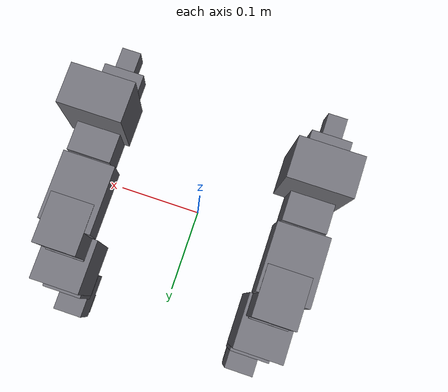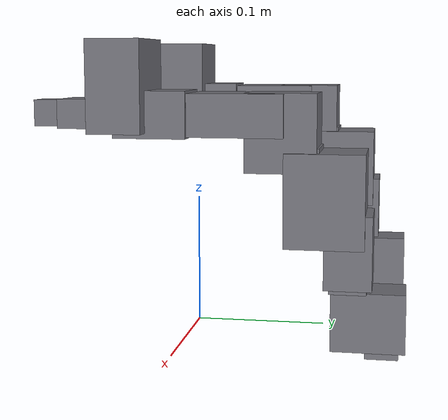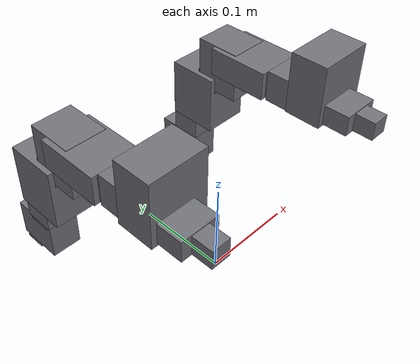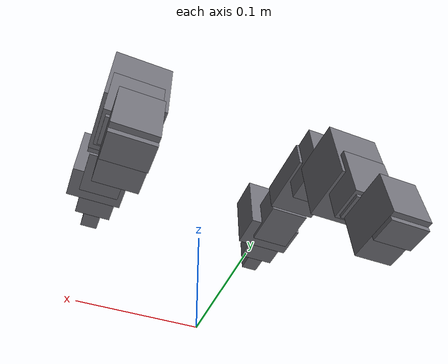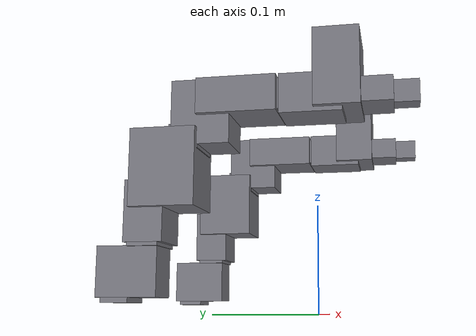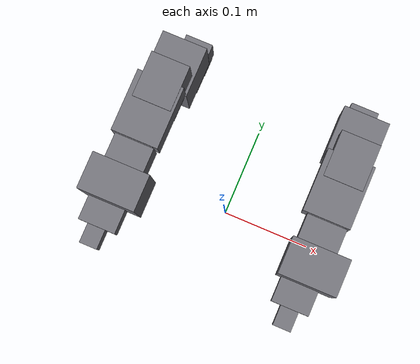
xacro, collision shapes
<robot xmlns:xacro="http://ros.org/wiki/xacro" name="dual_arm">
  <xacro:arg name="mode" default="mock" />
  <xacro:arg name="port" default="/dev/ttyUSB0" />
  <xacro:arg name="calibration_file" default="" />
  <xacro:arg name="enable_motion" default="false" />
  <link name="world" />
  <link name="arm1_base_link">
    <inertial>
      <mass value="0.1" />
      <inertia ixx="0.0001" iyy="0.0001" izz="0.0001" ixy="0" ixz="0" iyz="0" />
    </inertial>
    <visual name="component_1">
      <origin xyz="-0.1 0.11725 0" rpy="1.5707963267948966 0 0" />
      <geometry>
        <mesh filename="package://dual_arm_description/meshes/cad/component_001.stl" scale="0.001 0.001 0.001" />
      </geometry>
      <material name="cad_1">
        <color rgba="0.45 0.45 0.48 1" />
      </material>
    </visual>
    <visual name="component_2">
      <origin xyz="-0.1 0.11725 0" rpy="1.5707963267948966 0 0" />
      <geometry>
        <mesh filename="package://dual_arm_description/meshes/cad/component_002.stl" scale="0.001 0.001 0.001" />
      </geometry>
      <material name="cad_2">
        <color rgba="0.08 0.08 0.09 1" />
      </material>
    </visual>
    <visual name="component_20">
      <origin xyz="-0.1 0.11725 0" rpy="1.5707963267948966 0 0" />
      <geometry>
        <mesh filename="package://dual_arm_description/meshes/cad/component_020.stl" scale="0.001 0.001 0.001" />
      </geometry>
      <material name="cad_20">
        <color rgba="0.45 0.45 0.48 1" />
      </material>
    </visual>
    <visual name="component_21">
      <origin xyz="-0.1 0.11725 0" rpy="1.5707963267948966 0 0" />
      <geometry>
        <mesh filename="package://dual_arm_description/meshes/cad/component_021.stl" scale="0.001 0.001 0.001" />
      </geometry>
      <material name="cad_21">
        <color rgba="0.45 0.45 0.48 1" />
      </material>
    </visual>
    <visual name="component_22">
      <origin xyz="-0.1 0.11725 0" rpy="1.5707963267948966 0 0" />
      <geometry>
        <mesh filename="package://dual_arm_description/meshes/cad/component_022.stl" scale="0.001 0.001 0.001" />
      </geometry>
      <material name="cad_22">
        <color rgba="0.45 0.45 0.48 1" />
      </material>
    </visual>
    <visual name="component_23">
      <origin xyz="-0.1 0.11725 0" rpy="1.5707963267948966 0 0" />
      <geometry>
        <mesh filename="package://dual_arm_description/meshes/cad/component_023.stl" scale="0.001 0.001 0.001" />
      </geometry>
      <material name="cad_23">
        <color rgba="0.45 0.45 0.48 1" />
      </material>
    </visual>
    <visual name="component_24">
      <origin xyz="-0.1 0.11725 0" rpy="1.5707963267948966 0 0" />
      <geometry>
        <mesh filename="package://dual_arm_description/meshes/cad/component_024.stl" scale="0.001 0.001 0.001" />
      </geometry>
      <material name="cad_24">
        <color rgba="0.45 0.45 0.48 1" />
      </material>
    </visual>
    <visual name="component_25">
      <origin xyz="-0.1 0.11725 0" rpy="1.5707963267948966 0 0" />
      <geometry>
        <mesh filename="package://dual_arm_description/meshes/cad/component_025.stl" scale="0.001 0.001 0.001" />
      </geometry>
      <material name="cad_25">
        <color rgba="0.45 0.45 0.48 1" />
      </material>
    </visual>
    <visual name="component_26">
      <origin xyz="-0.1 0.11725 0" rpy="1.5707963267948966 0 0" />
      <geometry>
        <mesh filename="package://dual_arm_description/meshes/cad/component_026.stl" scale="0.001 0.001 0.001" />
      </geometry>
      <material name="cad_26">
        <color rgba="0.45 0.45 0.48 1" />
      </material>
    </visual>
    <visual name="component_27">
      <origin xyz="-0.1 0.11725 0" rpy="1.5707963267948966 0 0" />
      <geometry>
        <mesh filename="package://dual_arm_description/meshes/cad/component_027.stl" scale="0.001 0.001 0.001" />
      </geometry>
      <material name="cad_27">
        <color rgba="0.45 0.45 0.48 1" />
      </material>
    </visual>
    <visual name="component_28">
      <origin xyz="-0.1 0.11725 0" rpy="1.5707963267948966 0 0" />
      <geometry>
        <mesh filename="package://dual_arm_description/meshes/cad/component_028.stl" scale="0.001 0.001 0.001" />
      </geometry>
      <material name="cad_28">
        <color rgba="0.45 0.45 0.48 1" />
      </material>
    </visual>
    <visual name="component_29">
      <origin xyz="-0.1 0.11725 0" rpy="1.5707963267948966 0 0" />
      <geometry>
        <mesh filename="package://dual_arm_description/meshes/cad/component_029.stl" scale="0.001 0.001 0.001" />
      </geometry>
      <material name="cad_29">
        <color rgba="0.45 0.45 0.48 1" />
      </material>
    </visual>
    <visual name="component_30">
      <origin xyz="-0.1 0.11725 0" rpy="1.5707963267948966 0 0" />
      <geometry>
        <mesh filename="package://dual_arm_description/meshes/cad/component_030.stl" scale="0.001 0.001 0.001" />
      </geometry>
      <material name="cad_30">
        <color rgba="0.45 0.45 0.48 1" />
      </material>
    </visual>
    <visual name="component_31">
      <origin xyz="-0.1 0.11725 0" rpy="1.5707963267948966 0 0" />
      <geometry>
        <mesh filename="package://dual_arm_description/meshes/cad/component_031.stl" scale="0.001 0.001 0.001" />
      </geometry>
      <material name="cad_31">
        <color rgba="0.45 0.45 0.48 1" />
      </material>
    </visual>
    <visual name="component_32">
      <origin xyz="-0.1 0.11725 0" rpy="1.5707963267948966 0 0" />
      <geometry>
        <mesh filename="package://dual_arm_description/meshes/cad/component_032.stl" scale="0.001 0.001 0.001" />
      </geometry>
      <material name="cad_32">
        <color rgba="0.45 0.45 0.48 1" />
      </material>
    </visual>
    <visual name="component_33">
      <origin xyz="-0.1 0.11725 0" rpy="1.5707963267948966 0 0" />
      <geometry>
        <mesh filename="package://dual_arm_description/meshes/cad/component_033.stl" scale="0.001 0.001 0.001" />
      </geometry>
      <material name="cad_33">
        <color rgba="0.45 0.45 0.48 1" />
      </material>
    </visual>
    <visual name="component_34">
      <origin xyz="-0.1 0.11725 0" rpy="1.5707963267948966 0 0" />
      <geometry>
        <mesh filename="package://dual_arm_description/meshes/cad/component_034.stl" scale="0.001 0.001 0.001" />
      </geometry>
      <material name="cad_34">
        <color rgba="0.45 0.45 0.48 1" />
      </material>
    </visual>
    <visual name="component_35">
      <origin xyz="-0.1 0.11725 0" rpy="1.5707963267948966 0 0" />
      <geometry>
        <mesh filename="package://dual_arm_description/meshes/cad/component_035.stl" scale="0.001 0.001 0.001" />
      </geometry>
      <material name="cad_35">
        <color rgba="0.45 0.45 0.48 1" />
      </material>
    </visual>
    <visual name="component_36">
      <origin xyz="-0.1 0.11725 0" rpy="1.5707963267948966 0 0" />
      <geometry>
        <mesh filename="package://dual_arm_description/meshes/cad/component_036.stl" scale="0.001 0.001 0.001" />
      </geometry>
      <material name="cad_36">
        <color rgba="0.45 0.45 0.48 1" />
      </material>
    </visual>
    <visual name="component_37">
      <origin xyz="-0.1 0.11725 0" rpy="1.5707963267948966 0 0" />
      <geometry>
        <mesh filename="package://dual_arm_description/meshes/cad/component_037.stl" scale="0.001 0.001 0.001" />
      </geometry>
      <material name="cad_37">
        <color rgba="0.45 0.45 0.48 1" />
      </material>
    </visual>
    <visual name="component_38">
      <origin xyz="-0.1 0.11725 0" rpy="1.5707963267948966 0 0" />
      <geometry>
        <mesh filename="package://dual_arm_description/meshes/cad/component_038.stl" scale="0.001 0.001 0.001" />
      </geometry>
      <material name="cad_38">
        <color rgba="0.45 0.45 0.48 1" />
      </material>
    </visual>
    <visual name="component_39">
      <origin xyz="-0.1 0.11725 0" rpy="1.5707963267948966 0 0" />
      <geometry>
        <mesh filename="package://dual_arm_description/meshes/cad/component_039.stl" scale="0.001 0.001 0.001" />
      </geometry>
      <material name="cad_39">
        <color rgba="0.45 0.45 0.48 1" />
      </material>
    </visual>
    <visual name="component_40">
      <origin xyz="-0.1 0.11725 0" rpy="1.5707963267948966 0 0" />
      <geometry>
        <mesh filename="package://dual_arm_description/meshes/cad/component_040.stl" scale="0.001 0.001 0.001" />
      </geometry>
      <material name="cad_40">
        <color rgba="0.45 0.45 0.48 1" />
      </material>
    </visual>
    <visual name="component_41">
      <origin xyz="-0.1 0.11725 0" rpy="1.5707963267948966 0 0" />
      <geometry>
        <mesh filename="package://dual_arm_description/meshes/cad/component_041.stl" scale="0.001 0.001 0.001" />
      </geometry>
      <material name="cad_41">
        <color rgba="0.45 0.45 0.48 1" />
      </material>
    </visual>
    <visual name="component_42">
      <origin xyz="-0.1 0.11725 0" rpy="1.5707963267948966 0 0" />
      <geometry>
        <mesh filename="package://dual_arm_description/meshes/cad/component_042.stl" scale="0.001 0.001 0.001" />
      </geometry>
      <material name="cad_42">
        <color rgba="0.45 0.45 0.48 1" />
      </material>
    </visual>
    <visual name="component_43">
      <origin xyz="-0.1 0.11725 0" rpy="1.5707963267948966 0 0" />
      <geometry>
        <mesh filename="package://dual_arm_description/meshes/cad/component_043.stl" scale="0.001 0.001 0.001" />
      </geometry>
      <material name="cad_43">
        <color rgba="0.45 0.45 0.48 1" />
      </material>
    </visual>
    <visual name="component_45">
      <origin xyz="-0.1 0.11725 0" rpy="1.5707963267948966 0 0" />
      <geometry>
        <mesh filename="package://dual_arm_description/meshes/cad/component_045.stl" scale="0.001 0.001 0.001" />
      </geometry>
      <material name="cad_45">
        <color rgba="0.45 0.45 0.48 1" />
      </material>
    </visual>
    <visual name="component_47">
      <origin xyz="-0.1 0.11725 0" rpy="1.5707963267948966 0 0" />
      <geometry>
        <mesh filename="package://dual_arm_description/meshes/cad/component_047.stl" scale="0.001 0.001 0.001" />
      </geometry>
      <material name="cad_47">
        <color rgba="0.45 0.45 0.48 1" />
      </material>
    </visual>
    <visual name="component_49">
      <origin xyz="-0.1 0.11725 0" rpy="1.5707963267948966 0 0" />
      <geometry>
        <mesh filename="package://dual_arm_description/meshes/cad/component_049.stl" scale="0.001 0.001 0.001" />
      </geometry>
      <material name="cad_49">
        <color rgba="0.45 0.45 0.48 1" />
      </material>
    </visual>
    <visual name="component_51">
      <origin xyz="-0.1 0.11725 0" rpy="1.5707963267948966 0 0" />
      <geometry>
        <mesh filename="package://dual_arm_description/meshes/cad/component_051.stl" scale="0.001 0.001 0.001" />
      </geometry>
      <material name="cad_51">
        <color rgba="0.45 0.45 0.48 1" />
      </material>
    </visual>
    <collision name="box_1">
      <origin xyz="0 -0.02275 0.0141" />
      <geometry>
        <box size="0.03200880504 0.02240880504 0.008208805044" />
      </geometry>
    </collision>
    <collision name="box_2">
      <origin xyz="0 -0.0135 0.03427282996" />
      <geometry>
        <box size="0.03203807454 0.05003807454 0.04058373446" />
      </geometry>
    </collision>
  </link>
  <joint name="arm1_mount" type="fixed">
    <parent link="world" />
    <child link="arm1_base_link" />
    <origin xyz="-0.1 0.125 0" rpy="0 0 3.141592653589793" />
  </joint>
  <link name="arm1_cad_link_1">
    <inertial>
      <mass value="0.08" />
      <inertia ixx="0.0001" iyy="0.0001" izz="0.0001" ixy="0" ixz="0" iyz="0" />
    </inertial>
    <visual name="component_3">
      <origin xyz="-0.1 0.11725 -0.0485" rpy="1.5707963267948966 0 0" />
      <geometry>
        <mesh filename="package://dual_arm_description/meshes/cad/component_003.stl" scale="0.001 0.001 0.001" />
      </geometry>
      <material name="cad_3">
        <color rgba="0.45 0.45 0.48 1" />
      </material>
    </visual>
    <visual name="component_4">
      <origin xyz="-0.1 0.11725 -0.0485" rpy="1.5707963267948966 0 0" />
      <geometry>
        <mesh filename="package://dual_arm_description/meshes/cad/component_004.stl" scale="0.001 0.001 0.001" />
      </geometry>
      <material name="cad_4">
        <color rgba="0.08 0.08 0.09 1" />
      </material>
    </visual>
    <visual name="component_44">
      <origin xyz="-0.1 0.11725 -0.0485" rpy="1.5707963267948966 0 0" />
      <geometry>
        <mesh filename="package://dual_arm_description/meshes/cad/component_044.stl" scale="0.001 0.001 0.001" />
      </geometry>
      <material name="cad_44">
        <color rgba="0.45 0.45 0.48 1" />
      </material>
    </visual>
    <visual name="component_46">
      <origin xyz="-0.1 0.11725 -0.0485" rpy="1.5707963267948966 0 0" />
      <geometry>
        <mesh filename="package://dual_arm_description/meshes/cad/component_046.stl" scale="0.001 0.001 0.001" />
      </geometry>
      <material name="cad_46">
        <color rgba="0.45 0.45 0.48 1" />
      </material>
    </visual>
    <visual name="component_48">
      <origin xyz="-0.1 0.11725 -0.0485" rpy="1.5707963267948966 0 0" />
      <geometry>
        <mesh filename="package://dual_arm_description/meshes/cad/component_048.stl" scale="0.001 0.001 0.001" />
      </geometry>
      <material name="cad_48">
        <color rgba="0.45 0.45 0.48 1" />
      </material>
    </visual>
    <visual name="component_50">
      <origin xyz="-0.1 0.11725 -0.0485" rpy="1.5707963267948966 0 0" />
      <geometry>
        <mesh filename="package://dual_arm_description/meshes/cad/component_050.stl" scale="0.001 0.001 0.001" />
      </geometry>
      <material name="cad_50">
        <color rgba="0.45 0.45 0.48 1" />
      </material>
    </visual>
    <visual name="component_53">
      <origin xyz="-0.1 0.11725 -0.0485" rpy="1.5707963267948966 0 0" />
      <geometry>
        <mesh filename="package://dual_arm_description/meshes/cad/component_053.stl" scale="0.001 0.001 0.001" />
      </geometry>
      <material name="cad_53">
        <color rgba="0.45 0.45 0.48 1" />
      </material>
    </visual>
    <visual name="component_55">
      <origin xyz="-0.1 0.11725 -0.0485" rpy="1.5707963267948966 0 0" />
      <geometry>
        <mesh filename="package://dual_arm_description/meshes/cad/component_055.stl" scale="0.001 0.001 0.001" />
      </geometry>
      <material name="cad_55">
        <color rgba="0.45 0.45 0.48 1" />
      </material>
    </visual>
    <visual name="component_57">
      <origin xyz="-0.1 0.11725 -0.0485" rpy="1.5707963267948966 0 0" />
      <geometry>
        <mesh filename="package://dual_arm_description/meshes/cad/component_057.stl" scale="0.001 0.001 0.001" />
      </geometry>
      <material name="cad_57">
        <color rgba="0.45 0.45 0.48 1" />
      </material>
    </visual>
    <visual name="component_59">
      <origin xyz="-0.1 0.11725 -0.0485" rpy="1.5707963267948966 0 0" />
      <geometry>
        <mesh filename="package://dual_arm_description/meshes/cad/component_059.stl" scale="0.001 0.001 0.001" />
      </geometry>
      <material name="cad_59">
        <color rgba="0.45 0.45 0.48 1" />
      </material>
    </visual>
    <visual name="component_72">
      <origin xyz="-0.1 0.11725 -0.0485" rpy="1.5707963267948966 0 0" />
      <geometry>
        <mesh filename="package://dual_arm_description/meshes/cad/component_072.stl" scale="0.001 0.001 0.001" />
      </geometry>
      <material name="cad_72">
        <color rgba="0.45 0.45 0.48 1" />
      </material>
    </visual>
    <visual name="component_73">
      <origin xyz="-0.1 0.11725 -0.0485" rpy="1.5707963267948966 0 0" />
      <geometry>
        <mesh filename="package://dual_arm_description/meshes/cad/component_073.stl" scale="0.001 0.001 0.001" />
      </geometry>
      <material name="cad_73">
        <color rgba="0.45 0.45 0.48 1" />
      </material>
    </visual>
    <visual name="component_74">
      <origin xyz="-0.1 0.11725 -0.0485" rpy="1.5707963267948966 0 0" />
      <geometry>
        <mesh filename="package://dual_arm_description/meshes/cad/component_074.stl" scale="0.001 0.001 0.001" />
      </geometry>
      <material name="cad_74">
        <color rgba="0.45 0.45 0.48 1" />
      </material>
    </visual>
    <visual name="component_75">
      <origin xyz="-0.1 0.11725 -0.0485" rpy="1.5707963267948966 0 0" />
      <geometry>
        <mesh filename="package://dual_arm_description/meshes/cad/component_075.stl" scale="0.001 0.001 0.001" />
      </geometry>
      <material name="cad_75">
        <color rgba="0.45 0.45 0.48 1" />
      </material>
    </visual>
    <visual name="component_76">
      <origin xyz="-0.1 0.11725 -0.0485" rpy="1.5707963267948966 0 0" />
      <geometry>
        <mesh filename="package://dual_arm_description/meshes/cad/component_076.stl" scale="0.001 0.001 0.001" />
      </geometry>
      <material name="cad_76">
        <color rgba="0.45 0.45 0.48 1" />
      </material>
    </visual>
    <visual name="component_77">
      <origin xyz="-0.1 0.11725 -0.0485" rpy="1.5707963267948966 0 0" />
      <geometry>
        <mesh filename="package://dual_arm_description/meshes/cad/component_077.stl" scale="0.001 0.001 0.001" />
      </geometry>
      <material name="cad_77">
        <color rgba="0.45 0.45 0.48 1" />
      </material>
    </visual>
    <visual name="component_78">
      <origin xyz="-0.1 0.11725 -0.0485" rpy="1.5707963267948966 0 0" />
      <geometry>
        <mesh filename="package://dual_arm_description/meshes/cad/component_078.stl" scale="0.001 0.001 0.001" />
      </geometry>
      <material name="cad_78">
        <color rgba="0.45 0.45 0.48 1" />
      </material>
    </visual>
    <visual name="component_79">
      <origin xyz="-0.1 0.11725 -0.0485" rpy="1.5707963267948966 0 0" />
      <geometry>
        <mesh filename="package://dual_arm_description/meshes/cad/component_079.stl" scale="0.001 0.001 0.001" />
      </geometry>
      <material name="cad_79">
        <color rgba="0.45 0.45 0.48 1" />
      </material>
    </visual>
    <visual name="component_80">
      <origin xyz="-0.1 0.11725 -0.0485" rpy="1.5707963267948966 0 0" />
      <geometry>
        <mesh filename="package://dual_arm_description/meshes/cad/component_080.stl" scale="0.001 0.001 0.001" />
      </geometry>
      <material name="cad_80">
        <color rgba="0.45 0.45 0.48 1" />
      </material>
    </visual>
    <visual name="component_81">
      <origin xyz="-0.1 0.11725 -0.0485" rpy="1.5707963267948966 0 0" />
      <geometry>
        <mesh filename="package://dual_arm_description/meshes/cad/component_081.stl" scale="0.001 0.001 0.001" />
      </geometry>
      <material name="cad_81">
        <color rgba="0.45 0.45 0.48 1" />
      </material>
    </visual>
    <visual name="component_82">
      <origin xyz="-0.1 0.11725 -0.0485" rpy="1.5707963267948966 0 0" />
      <geometry>
        <mesh filename="package://dual_arm_description/meshes/cad/component_082.stl" scale="0.001 0.001 0.001" />
      </geometry>
      <material name="cad_82">
        <color rgba="0.45 0.45 0.48 1" />
      </material>
    </visual>
    <visual name="component_83">
      <origin xyz="-0.1 0.11725 -0.0485" rpy="1.5707963267948966 0 0" />
      <geometry>
        <mesh filename="package://dual_arm_description/meshes/cad/component_083.stl" scale="0.001 0.001 0.001" />
      </geometry>
      <material name="cad_83">
        <color rgba="0.45 0.45 0.48 1" />
      </material>
    </visual>
    <collision name="box_3">
      <origin xyz="0 -2.081668171e-16 0.01" />
      <geometry>
        <box size="0.03800928453 0.02500928453 0.009009284533" />
      </geometry>
    </collision>
    <collision name="box_4">
      <origin xyz="-0.001272829961 0 0.0335" />
      <geometry>
        <box size="0.04058373446 0.03203807454 0.05003807454" />
      </geometry>
    </collision>
  </link>
  <joint name="arm1_arm_shoulder_pan_joint" type="revolute">
    <parent link="arm1_base_link" />
    <child link="arm1_cad_link_1" />
    <origin xyz="0 0 0.0485" />
    <axis xyz="0 0 1" />
    <limit lower="-1.5" upper="1.5" effort="1.5" velocity="0.5" />
    <dynamics damping="0.05" friction="0.01" />
  </joint>
  <link name="arm1_cad_link_2">
    <inertial>
      <mass value="0.08" />
      <inertia ixx="0.0001" iyy="0.0001" izz="0.0001" ixy="0" ixz="0" iyz="0" />
    </inertial>
    <visual name="component_5">
      <origin xyz="-0.0845 0.11725 -0.0955" rpy="1.5707963267948966 0 0" />
      <geometry>
        <mesh filename="package://dual_arm_description/meshes/cad/component_005.stl" scale="0.001 0.001 0.001" />
      </geometry>
      <material name="cad_5">
        <color rgba="0.45 0.45 0.48 1" />
      </material>
    </visual>
    <visual name="component_6">
      <origin xyz="-0.0845 0.11725 -0.0955" rpy="1.5707963267948966 0 0" />
      <geometry>
        <mesh filename="package://dual_arm_description/meshes/cad/component_006.stl" scale="0.001 0.001 0.001" />
      </geometry>
      <material name="cad_6">
        <color rgba="0.45 0.45 0.48 1" />
      </material>
    </visual>
    <visual name="component_7">
      <origin xyz="-0.0845 0.11725 -0.0955" rpy="1.5707963267948966 0 0" />
      <geometry>
        <mesh filename="package://dual_arm_description/meshes/cad/component_007.stl" scale="0.001 0.001 0.001" />
      </geometry>
      <material name="cad_7">
        <color rgba="0.08 0.08 0.09 1" />
      </material>
    </visual>
    <visual name="component_52">
      <origin xyz="-0.0845 0.11725 -0.0955" rpy="1.5707963267948966 0 0" />
      <geometry>
        <mesh filename="package://dual_arm_description/meshes/cad/component_052.stl" scale="0.001 0.001 0.001" />
      </geometry>
      <material name="cad_52">
        <color rgba="0.45 0.45 0.48 1" />
      </material>
    </visual>
    <visual name="component_54">
      <origin xyz="-0.0845 0.11725 -0.0955" rpy="1.5707963267948966 0 0" />
      <geometry>
        <mesh filename="package://dual_arm_description/meshes/cad/component_054.stl" scale="0.001 0.001 0.001" />
      </geometry>
      <material name="cad_54">
        <color rgba="0.45 0.45 0.48 1" />
      </material>
    </visual>
    <visual name="component_56">
      <origin xyz="-0.0845 0.11725 -0.0955" rpy="1.5707963267948966 0 0" />
      <geometry>
        <mesh filename="package://dual_arm_description/meshes/cad/component_056.stl" scale="0.001 0.001 0.001" />
      </geometry>
      <material name="cad_56">
        <color rgba="0.45 0.45 0.48 1" />
      </material>
    </visual>
    <visual name="component_58">
      <origin xyz="-0.0845 0.11725 -0.0955" rpy="1.5707963267948966 0 0" />
      <geometry>
        <mesh filename="package://dual_arm_description/meshes/cad/component_058.stl" scale="0.001 0.001 0.001" />
      </geometry>
      <material name="cad_58">
        <color rgba="0.45 0.45 0.48 1" />
      </material>
    </visual>
    <visual name="component_61">
      <origin xyz="-0.0845 0.11725 -0.0955" rpy="1.5707963267948966 0 0" />
      <geometry>
        <mesh filename="package://dual_arm_description/meshes/cad/component_061.stl" scale="0.001 0.001 0.001" />
      </geometry>
      <material name="cad_61">
        <color rgba="0.45 0.45 0.48 1" />
      </material>
    </visual>
    <visual name="component_63">
      <origin xyz="-0.0845 0.11725 -0.0955" rpy="1.5707963267948966 0 0" />
      <geometry>
        <mesh filename="package://dual_arm_description/meshes/cad/component_063.stl" scale="0.001 0.001 0.001" />
      </geometry>
      <material name="cad_63">
        <color rgba="0.45 0.45 0.48 1" />
      </material>
    </visual>
    <visual name="component_65">
      <origin xyz="-0.0845 0.11725 -0.0955" rpy="1.5707963267948966 0 0" />
      <geometry>
        <mesh filename="package://dual_arm_description/meshes/cad/component_065.stl" scale="0.001 0.001 0.001" />
      </geometry>
      <material name="cad_65">
        <color rgba="0.45 0.45 0.48 1" />
      </material>
    </visual>
    <visual name="component_67">
      <origin xyz="-0.0845 0.11725 -0.0955" rpy="1.5707963267948966 0 0" />
      <geometry>
        <mesh filename="package://dual_arm_description/meshes/cad/component_067.stl" scale="0.001 0.001 0.001" />
      </geometry>
      <material name="cad_67">
        <color rgba="0.45 0.45 0.48 1" />
      </material>
    </visual>
    <visual name="component_68">
      <origin xyz="-0.0845 0.11725 -0.0955" rpy="1.5707963267948966 0 0" />
      <geometry>
        <mesh filename="package://dual_arm_description/meshes/cad/component_068.stl" scale="0.001 0.001 0.001" />
      </geometry>
      <material name="cad_68">
        <color rgba="0.45 0.45 0.48 1" />
      </material>
    </visual>
    <visual name="component_69">
      <origin xyz="-0.0845 0.11725 -0.0955" rpy="1.5707963267948966 0 0" />
      <geometry>
        <mesh filename="package://dual_arm_description/meshes/cad/component_069.stl" scale="0.001 0.001 0.001" />
      </geometry>
      <material name="cad_69">
        <color rgba="0.45 0.45 0.48 1" />
      </material>
    </visual>
    <visual name="component_84">
      <origin xyz="-0.0845 0.11725 -0.0955" rpy="1.5707963267948966 0 0" />
      <geometry>
        <mesh filename="package://dual_arm_description/meshes/cad/component_084.stl" scale="0.001 0.001 0.001" />
      </geometry>
      <material name="cad_84">
        <color rgba="0.45 0.45 0.48 1" />
      </material>
    </visual>
    <visual name="component_85">
      <origin xyz="-0.0845 0.11725 -0.0955" rpy="1.5707963267948966 0 0" />
      <geometry>
        <mesh filename="package://dual_arm_description/meshes/cad/component_085.stl" scale="0.001 0.001 0.001" />
      </geometry>
      <material name="cad_85">
        <color rgba="0.45 0.45 0.48 1" />
      </material>
    </visual>
    <visual name="component_86">
      <origin xyz="-0.0845 0.11725 -0.0955" rpy="1.5707963267948966 0 0" />
      <geometry>
        <mesh filename="package://dual_arm_description/meshes/cad/component_086.stl" scale="0.001 0.001 0.001" />
      </geometry>
      <material name="cad_86">
        <color rgba="0.45 0.45 0.48 1" />
      </material>
    </visual>
    <visual name="component_87">
      <origin xyz="-0.0845 0.11725 -0.0955" rpy="1.5707963267948966 0 0" />
      <geometry>
        <mesh filename="package://dual_arm_description/meshes/cad/component_087.stl" scale="0.001 0.001 0.001" />
      </geometry>
      <material name="cad_87">
        <color rgba="0.45 0.45 0.48 1" />
      </material>
    </visual>
    <visual name="component_88">
      <origin xyz="-0.0845 0.11725 -0.0955" rpy="1.5707963267948966 0 0" />
      <geometry>
        <mesh filename="package://dual_arm_description/meshes/cad/component_088.stl" scale="0.001 0.001 0.001" />
      </geometry>
      <material name="cad_88">
        <color rgba="0.45 0.45 0.48 1" />
      </material>
    </visual>
    <visual name="component_89">
      <origin xyz="-0.0845 0.11725 -0.0955" rpy="1.5707963267948966 0 0" />
      <geometry>
        <mesh filename="package://dual_arm_description/meshes/cad/component_089.stl" scale="0.001 0.001 0.001" />
      </geometry>
      <material name="cad_89">
        <color rgba="0.45 0.45 0.48 1" />
      </material>
    </visual>
    <visual name="component_90">
      <origin xyz="-0.0845 0.11725 -0.0955" rpy="1.5707963267948966 0 0" />
      <geometry>
        <mesh filename="package://dual_arm_description/meshes/cad/component_090.stl" scale="0.001 0.001 0.001" />
      </geometry>
      <material name="cad_90">
        <color rgba="0.45 0.45 0.48 1" />
      </material>
    </visual>
    <visual name="component_91">
      <origin xyz="-0.0845 0.11725 -0.0955" rpy="1.5707963267948966 0 0" />
      <geometry>
        <mesh filename="package://dual_arm_description/meshes/cad/component_091.stl" scale="0.001 0.001 0.001" />
      </geometry>
      <material name="cad_91">
        <color rgba="0.45 0.45 0.48 1" />
      </material>
    </visual>
    <visual name="component_92">
      <origin xyz="-0.0845 0.11725 -0.0955" rpy="1.5707963267948966 0 0" />
      <geometry>
        <mesh filename="package://dual_arm_description/meshes/cad/component_092.stl" scale="0.001 0.001 0.001" />
      </geometry>
      <material name="cad_92">
        <color rgba="0.45 0.45 0.48 1" />
      </material>
    </visual>
    <visual name="component_93">
      <origin xyz="-0.0845 0.11725 -0.0955" rpy="1.5707963267948966 0 0" />
      <geometry>
        <mesh filename="package://dual_arm_description/meshes/cad/component_093.stl" scale="0.001 0.001 0.001" />
      </geometry>
      <material name="cad_93">
        <color rgba="0.45 0.45 0.48 1" />
      </material>
    </visual>
    <visual name="component_94">
      <origin xyz="-0.0845 0.11725 -0.0955" rpy="1.5707963267948966 0 0" />
      <geometry>
        <mesh filename="package://dual_arm_description/meshes/cad/component_094.stl" scale="0.001 0.001 0.001" />
      </geometry>
      <material name="cad_94">
        <color rgba="0.45 0.45 0.48 1" />
      </material>
    </visual>
    <visual name="component_95">
      <origin xyz="-0.0845 0.11725 -0.0955" rpy="1.5707963267948966 0 0" />
      <geometry>
        <mesh filename="package://dual_arm_description/meshes/cad/component_095.stl" scale="0.001 0.001 0.001" />
      </geometry>
      <material name="cad_95">
        <color rgba="0.45 0.45 0.48 1" />
      </material>
    </visual>
    <visual name="component_108">
      <origin xyz="-0.0845 0.11725 -0.0955" rpy="1.5707963267948966 0 0" />
      <geometry>
        <mesh filename="package://dual_arm_description/meshes/cad/component_108.stl" scale="0.001 0.001 0.001" />
      </geometry>
      <material name="cad_108">
        <color rgba="0.45 0.45 0.48 1" />
      </material>
    </visual>
    <visual name="component_109">
      <origin xyz="-0.0845 0.11725 -0.0955" rpy="1.5707963267948966 0 0" />
      <geometry>
        <mesh filename="package://dual_arm_description/meshes/cad/component_109.stl" scale="0.001 0.001 0.001" />
      </geometry>
      <material name="cad_109">
        <color rgba="0.45 0.45 0.48 1" />
      </material>
    </visual>
    <visual name="component_110">
      <origin xyz="-0.0845 0.11725 -0.0955" rpy="1.5707963267948966 0 0" />
      <geometry>
        <mesh filename="package://dual_arm_description/meshes/cad/component_110.stl" scale="0.001 0.001 0.001" />
      </geometry>
      <material name="cad_110">
        <color rgba="0.45 0.45 0.48 1" />
      </material>
    </visual>
    <visual name="component_111">
      <origin xyz="-0.0845 0.11725 -0.0955" rpy="1.5707963267948966 0 0" />
      <geometry>
        <mesh filename="package://dual_arm_description/meshes/cad/component_111.stl" scale="0.001 0.001 0.001" />
      </geometry>
      <material name="cad_111">
        <color rgba="0.45 0.45 0.48 1" />
      </material>
    </visual>
    <visual name="component_112">
      <origin xyz="-0.0845 0.11725 -0.0955" rpy="1.5707963267948966 0 0" />
      <geometry>
        <mesh filename="package://dual_arm_description/meshes/cad/component_112.stl" scale="0.001 0.001 0.001" />
      </geometry>
      <material name="cad_112">
        <color rgba="0.45 0.45 0.48 1" />
      </material>
    </visual>
    <visual name="component_113">
      <origin xyz="-0.0845 0.11725 -0.0955" rpy="1.5707963267948966 0 0" />
      <geometry>
        <mesh filename="package://dual_arm_description/meshes/cad/component_113.stl" scale="0.001 0.001 0.001" />
      </geometry>
      <material name="cad_113">
        <color rgba="0.45 0.45 0.48 1" />
      </material>
    </visual>
    <visual name="component_114">
      <origin xyz="-0.0845 0.11725 -0.0955" rpy="1.5707963267948966 0 0" />
      <geometry>
        <mesh filename="package://dual_arm_description/meshes/cad/component_114.stl" scale="0.001 0.001 0.001" />
      </geometry>
      <material name="cad_114">
        <color rgba="0.45 0.45 0.48 1" />
      </material>
    </visual>
    <visual name="component_115">
      <origin xyz="-0.0845 0.11725 -0.0955" rpy="1.5707963267948966 0 0" />
      <geometry>
        <mesh filename="package://dual_arm_description/meshes/cad/component_115.stl" scale="0.001 0.001 0.001" />
      </geometry>
      <material name="cad_115">
        <color rgba="0.45 0.45 0.48 1" />
      </material>
    </visual>
    <visual name="component_116">
      <origin xyz="-0.0845 0.11725 -0.0955" rpy="1.5707963267948966 0 0" />
      <geometry>
        <mesh filename="package://dual_arm_description/meshes/cad/component_116.stl" scale="0.001 0.001 0.001" />
      </geometry>
      <material name="cad_116">
        <color rgba="0.45 0.45 0.48 1" />
      </material>
    </visual>
    <visual name="component_117">
      <origin xyz="-0.0845 0.11725 -0.0955" rpy="1.5707963267948966 0 0" />
      <geometry>
        <mesh filename="package://dual_arm_description/meshes/cad/component_117.stl" scale="0.001 0.001 0.001" />
      </geometry>
      <material name="cad_117">
        <color rgba="0.45 0.45 0.48 1" />
      </material>
    </visual>
    <visual name="component_118">
      <origin xyz="-0.0845 0.11725 -0.0955" rpy="1.5707963267948966 0 0" />
      <geometry>
        <mesh filename="package://dual_arm_description/meshes/cad/component_118.stl" scale="0.001 0.001 0.001" />
      </geometry>
      <material name="cad_118">
        <color rgba="0.45 0.45 0.48 1" />
      </material>
    </visual>
    <visual name="component_119">
      <origin xyz="-0.0845 0.11725 -0.0955" rpy="1.5707963267948966 0 0" />
      <geometry>
        <mesh filename="package://dual_arm_description/meshes/cad/component_119.stl" scale="0.001 0.001 0.001" />
      </geometry>
      <material name="cad_119">
        <color rgba="0.45 0.45 0.48 1" />
      </material>
    </visual>
    <collision name="box_5">
      <origin xyz="0.0155 0.01583950566 0.02065271228" />
      <geometry>
        <box size="0.04882558756 0.05370409479 0.0633308092" />
      </geometry>
    </collision>
    <collision name="box_6">
      <origin xyz="0.0155 0.031546704 0.04542172585" />
      <geometry>
        <box size="0.03800928453 0.02392954426 0.02000033453" />
      </geometry>
    </collision>
    <collision name="box_7">
      <origin xyz="0.01422717004 0.04496596926 0.06505162679" />
      <geometry>
        <box size="0.04058373446 0.04792728255 0.05294007307" />
      </geometry>
    </collision>
  </link>
  <joint name="arm1_arm_shoulder_lift_joint" type="revolute">
    <parent link="arm1_cad_link_1" />
    <child link="arm1_cad_link_2" />
    <origin xyz="-0.0155 0 0.047" />
    <axis xyz="-1 0 0" />
    <limit lower="-1.5" upper="1.5" effort="1.5" velocity="0.5" />
    <dynamics damping="0.05" friction="0.01" />
  </joint>
  <link name="arm1_cad_link_3">
    <inertial>
      <mass value="0.08" />
      <inertia ixx="0.0001" iyy="0.0001" izz="0.0001" ixy="0" ixz="0" iyz="0" />
    </inertial>
    <visual name="component_8">
      <origin xyz="-0.0845 0.0636206032 -0.1720907161" rpy="1.5707963267948966 0 0" />
      <geometry>
        <mesh filename="package://dual_arm_description/meshes/cad/component_008.stl" scale="0.001 0.001 0.001" />
      </geometry>
      <material name="cad_8">
        <color rgba="0.45 0.45 0.48 1" />
      </material>
    </visual>
    <visual name="component_9">
      <origin xyz="-0.0845 0.0636206032 -0.1720907161" rpy="1.5707963267948966 0 0" />
      <geometry>
        <mesh filename="package://dual_arm_description/meshes/cad/component_009.stl" scale="0.001 0.001 0.001" />
      </geometry>
      <material name="cad_9">
        <color rgba="0.45 0.45 0.48 1" />
      </material>
    </visual>
    <visual name="component_12">
      <origin xyz="-0.0845 0.0636206032 -0.1720907161" rpy="1.5707963267948966 0 0" />
      <geometry>
        <mesh filename="package://dual_arm_description/meshes/cad/component_012.stl" scale="0.001 0.001 0.001" />
      </geometry>
      <material name="cad_12">
        <color rgba="0.08 0.08 0.09 1" />
      </material>
    </visual>
    <visual name="component_13">
      <origin xyz="-0.0845 0.0636206032 -0.1720907161" rpy="1.5707963267948966 0 0" />
      <geometry>
        <mesh filename="package://dual_arm_description/meshes/cad/component_013.stl" scale="0.001 0.001 0.001" />
      </geometry>
      <material name="cad_13">
        <color rgba="0.45 0.45 0.48 1" />
      </material>
    </visual>
    <visual name="component_14">
      <origin xyz="-0.0845 0.0636206032 -0.1720907161" rpy="1.5707963267948966 0 0" />
      <geometry>
        <mesh filename="package://dual_arm_description/meshes/cad/component_014.stl" scale="0.001 0.001 0.001" />
      </geometry>
      <material name="cad_14">
        <color rgba="0.45 0.45 0.48 1" />
      </material>
    </visual>
    <visual name="component_15">
      <origin xyz="-0.0845 0.0636206032 -0.1720907161" rpy="1.5707963267948966 0 0" />
      <geometry>
        <mesh filename="package://dual_arm_description/meshes/cad/component_015.stl" scale="0.001 0.001 0.001" />
      </geometry>
      <material name="cad_15">
        <color rgba="0.45 0.45 0.48 1" />
      </material>
    </visual>
    <visual name="component_16">
      <origin xyz="-0.0845 0.0636206032 -0.1720907161" rpy="1.5707963267948966 0 0" />
      <geometry>
        <mesh filename="package://dual_arm_description/meshes/cad/component_016.stl" scale="0.001 0.001 0.001" />
      </geometry>
      <material name="cad_16">
        <color rgba="0.45 0.45 0.48 1" />
      </material>
    </visual>
    <visual name="component_60">
      <origin xyz="-0.0845 0.0636206032 -0.1720907161" rpy="1.5707963267948966 0 0" />
      <geometry>
        <mesh filename="package://dual_arm_description/meshes/cad/component_060.stl" scale="0.001 0.001 0.001" />
      </geometry>
      <material name="cad_60">
        <color rgba="0.45 0.45 0.48 1" />
      </material>
    </visual>
    <visual name="component_62">
      <origin xyz="-0.0845 0.0636206032 -0.1720907161" rpy="1.5707963267948966 0 0" />
      <geometry>
        <mesh filename="package://dual_arm_description/meshes/cad/component_062.stl" scale="0.001 0.001 0.001" />
      </geometry>
      <material name="cad_62">
        <color rgba="0.45 0.45 0.48 1" />
      </material>
    </visual>
    <visual name="component_64">
      <origin xyz="-0.0845 0.0636206032 -0.1720907161" rpy="1.5707963267948966 0 0" />
      <geometry>
        <mesh filename="package://dual_arm_description/meshes/cad/component_064.stl" scale="0.001 0.001 0.001" />
      </geometry>
      <material name="cad_64">
        <color rgba="0.45 0.45 0.48 1" />
      </material>
    </visual>
    <visual name="component_66">
      <origin xyz="-0.0845 0.0636206032 -0.1720907161" rpy="1.5707963267948966 0 0" />
      <geometry>
        <mesh filename="package://dual_arm_description/meshes/cad/component_066.stl" scale="0.001 0.001 0.001" />
      </geometry>
      <material name="cad_66">
        <color rgba="0.45 0.45 0.48 1" />
      </material>
    </visual>
    <visual name="component_70">
      <origin xyz="-0.0845 0.0636206032 -0.1720907161" rpy="1.5707963267948966 0 0" />
      <geometry>
        <mesh filename="package://dual_arm_description/meshes/cad/component_070.stl" scale="0.001 0.001 0.001" />
      </geometry>
      <material name="cad_70">
        <color rgba="0.45 0.45 0.48 1" />
      </material>
    </visual>
    <visual name="component_71">
      <origin xyz="-0.0845 0.0636206032 -0.1720907161" rpy="1.5707963267948966 0 0" />
      <geometry>
        <mesh filename="package://dual_arm_description/meshes/cad/component_071.stl" scale="0.001 0.001 0.001" />
      </geometry>
      <material name="cad_71">
        <color rgba="0.45 0.45 0.48 1" />
      </material>
    </visual>
    <visual name="component_96">
      <origin xyz="-0.0845 0.0636206032 -0.1720907161" rpy="1.5707963267948966 0 0" />
      <geometry>
        <mesh filename="package://dual_arm_description/meshes/cad/component_096.stl" scale="0.001 0.001 0.001" />
      </geometry>
      <material name="cad_96">
        <color rgba="0.45 0.45 0.48 1" />
      </material>
    </visual>
    <visual name="component_97">
      <origin xyz="-0.0845 0.0636206032 -0.1720907161" rpy="1.5707963267948966 0 0" />
      <geometry>
        <mesh filename="package://dual_arm_description/meshes/cad/component_097.stl" scale="0.001 0.001 0.001" />
      </geometry>
      <material name="cad_97">
        <color rgba="0.45 0.45 0.48 1" />
      </material>
    </visual>
    <visual name="component_98">
      <origin xyz="-0.0845 0.0636206032 -0.1720907161" rpy="1.5707963267948966 0 0" />
      <geometry>
        <mesh filename="package://dual_arm_description/meshes/cad/component_098.stl" scale="0.001 0.001 0.001" />
      </geometry>
      <material name="cad_98">
        <color rgba="0.45 0.45 0.48 1" />
      </material>
    </visual>
    <visual name="component_99">
      <origin xyz="-0.0845 0.0636206032 -0.1720907161" rpy="1.5707963267948966 0 0" />
      <geometry>
        <mesh filename="package://dual_arm_description/meshes/cad/component_099.stl" scale="0.001 0.001 0.001" />
      </geometry>
      <material name="cad_99">
        <color rgba="0.45 0.45 0.48 1" />
      </material>
    </visual>
    <visual name="component_100">
      <origin xyz="-0.0845 0.0636206032 -0.1720907161" rpy="1.5707963267948966 0 0" />
      <geometry>
        <mesh filename="package://dual_arm_description/meshes/cad/component_100.stl" scale="0.001 0.001 0.001" />
      </geometry>
      <material name="cad_100">
        <color rgba="0.45 0.45 0.48 1" />
      </material>
    </visual>
    <visual name="component_101">
      <origin xyz="-0.0845 0.0636206032 -0.1720907161" rpy="1.5707963267948966 0 0" />
      <geometry>
        <mesh filename="package://dual_arm_description/meshes/cad/component_101.stl" scale="0.001 0.001 0.001" />
      </geometry>
      <material name="cad_101">
        <color rgba="0.45 0.45 0.48 1" />
      </material>
    </visual>
    <visual name="component_102">
      <origin xyz="-0.0845 0.0636206032 -0.1720907161" rpy="1.5707963267948966 0 0" />
      <geometry>
        <mesh filename="package://dual_arm_description/meshes/cad/component_102.stl" scale="0.001 0.001 0.001" />
      </geometry>
      <material name="cad_102">
        <color rgba="0.45 0.45 0.48 1" />
      </material>
    </visual>
    <visual name="component_103">
      <origin xyz="-0.0845 0.0636206032 -0.1720907161" rpy="1.5707963267948966 0 0" />
      <geometry>
        <mesh filename="package://dual_arm_description/meshes/cad/component_103.stl" scale="0.001 0.001 0.001" />
      </geometry>
      <material name="cad_103">
        <color rgba="0.45 0.45 0.48 1" />
      </material>
    </visual>
    <visual name="component_104">
      <origin xyz="-0.0845 0.0636206032 -0.1720907161" rpy="1.5707963267948966 0 0" />
      <geometry>
        <mesh filename="package://dual_arm_description/meshes/cad/component_104.stl" scale="0.001 0.001 0.001" />
      </geometry>
      <material name="cad_104">
        <color rgba="0.45 0.45 0.48 1" />
      </material>
    </visual>
    <visual name="component_105">
      <origin xyz="-0.0845 0.0636206032 -0.1720907161" rpy="1.5707963267948966 0 0" />
      <geometry>
        <mesh filename="package://dual_arm_description/meshes/cad/component_105.stl" scale="0.001 0.001 0.001" />
      </geometry>
      <material name="cad_105">
        <color rgba="0.45 0.45 0.48 1" />
      </material>
    </visual>
    <visual name="component_106">
      <origin xyz="-0.0845 0.0636206032 -0.1720907161" rpy="1.5707963267948966 0 0" />
      <geometry>
        <mesh filename="package://dual_arm_description/meshes/cad/component_106.stl" scale="0.001 0.001 0.001" />
      </geometry>
      <material name="cad_106">
        <color rgba="0.45 0.45 0.48 1" />
      </material>
    </visual>
    <visual name="component_107">
      <origin xyz="-0.0845 0.0636206032 -0.1720907161" rpy="1.5707963267948966 0 0" />
      <geometry>
        <mesh filename="package://dual_arm_description/meshes/cad/component_107.stl" scale="0.001 0.001 0.001" />
      </geometry>
      <material name="cad_107">
        <color rgba="0.45 0.45 0.48 1" />
      </material>
    </visual>
    <visual name="component_120">
      <origin xyz="-0.0845 0.0636206032 -0.1720907161" rpy="1.5707963267948966 0 0" />
      <geometry>
        <mesh filename="package://dual_arm_description/meshes/cad/component_120.stl" scale="0.001 0.001 0.001" />
      </geometry>
      <material name="cad_120">
        <color rgba="0.45 0.45 0.48 1" />
      </material>
    </visual>
    <visual name="component_121">
      <origin xyz="-0.0845 0.0636206032 -0.1720907161" rpy="1.5707963267948966 0 0" />
      <geometry>
        <mesh filename="package://dual_arm_description/meshes/cad/component_121.stl" scale="0.001 0.001 0.001" />
      </geometry>
      <material name="cad_121">
        <color rgba="0.45 0.45 0.48 1" />
      </material>
    </visual>
    <visual name="component_122">
      <origin xyz="-0.0845 0.0636206032 -0.1720907161" rpy="1.5707963267948966 0 0" />
      <geometry>
        <mesh filename="package://dual_arm_description/meshes/cad/component_122.stl" scale="0.001 0.001 0.001" />
      </geometry>
      <material name="cad_122">
        <color rgba="0.45 0.45 0.48 1" />
      </material>
    </visual>
    <visual name="component_123">
      <origin xyz="-0.0845 0.0636206032 -0.1720907161" rpy="1.5707963267948966 0 0" />
      <geometry>
        <mesh filename="package://dual_arm_description/meshes/cad/component_123.stl" scale="0.001 0.001 0.001" />
      </geometry>
      <material name="cad_123">
        <color rgba="0.45 0.45 0.48 1" />
      </material>
    </visual>
    <visual name="component_124">
      <origin xyz="-0.0845 0.0636206032 -0.1720907161" rpy="1.5707963267948966 0 0" />
      <geometry>
        <mesh filename="package://dual_arm_description/meshes/cad/component_124.stl" scale="0.001 0.001 0.001" />
      </geometry>
      <material name="cad_124">
        <color rgba="0.45 0.45 0.48 1" />
      </material>
    </visual>
    <visual name="component_125">
      <origin xyz="-0.0845 0.0636206032 -0.1720907161" rpy="1.5707963267948966 0 0" />
      <geometry>
        <mesh filename="package://dual_arm_description/meshes/cad/component_125.stl" scale="0.001 0.001 0.001" />
      </geometry>
      <material name="cad_125">
        <color rgba="0.45 0.45 0.48 1" />
      </material>
    </visual>
    <visual name="component_126">
      <origin xyz="-0.0845 0.0636206032 -0.1720907161" rpy="1.5707963267948966 0 0" />
      <geometry>
        <mesh filename="package://dual_arm_description/meshes/cad/component_126.stl" scale="0.001 0.001 0.001" />
      </geometry>
      <material name="cad_126">
        <color rgba="0.45 0.45 0.48 1" />
      </material>
    </visual>
    <visual name="component_127">
      <origin xyz="-0.0845 0.0636206032 -0.1720907161" rpy="1.5707963267948966 0 0" />
      <geometry>
        <mesh filename="package://dual_arm_description/meshes/cad/component_127.stl" scale="0.001 0.001 0.001" />
      </geometry>
      <material name="cad_127">
        <color rgba="0.45 0.45 0.48 1" />
      </material>
    </visual>
    <visual name="component_128">
      <origin xyz="-0.0845 0.0636206032 -0.1720907161" rpy="1.5707963267948966 0 0" />
      <geometry>
        <mesh filename="package://dual_arm_description/meshes/cad/component_128.stl" scale="0.001 0.001 0.001" />
      </geometry>
      <material name="cad_128">
        <color rgba="0.45 0.45 0.48 1" />
      </material>
    </visual>
    <visual name="component_129">
      <origin xyz="-0.0845 0.0636206032 -0.1720907161" rpy="1.5707963267948966 0 0" />
      <geometry>
        <mesh filename="package://dual_arm_description/meshes/cad/component_129.stl" scale="0.001 0.001 0.001" />
      </geometry>
      <material name="cad_129">
        <color rgba="0.45 0.45 0.48 1" />
      </material>
    </visual>
    <visual name="component_130">
      <origin xyz="-0.0845 0.0636206032 -0.1720907161" rpy="1.5707963267948966 0 0" />
      <geometry>
        <mesh filename="package://dual_arm_description/meshes/cad/component_130.stl" scale="0.001 0.001 0.001" />
      </geometry>
      <material name="cad_130">
        <color rgba="0.45 0.45 0.48 1" />
      </material>
    </visual>
    <visual name="component_131">
      <origin xyz="-0.0845 0.0636206032 -0.1720907161" rpy="1.5707963267948966 0 0" />
      <geometry>
        <mesh filename="package://dual_arm_description/meshes/cad/component_131.stl" scale="0.001 0.001 0.001" />
      </geometry>
      <material name="cad_131">
        <color rgba="0.45 0.45 0.48 1" />
      </material>
    </visual>
    <collision name="box_8">
      <origin xyz="0.0155 0.02135002663 -5.551115123e-17" />
      <geometry>
        <box size="0.04882558756 0.06472553429 0.02902558756" />
      </geometry>
    </collision>
    <collision name="box_9">
      <origin xyz="0.0155 0.0565 1.665334537e-16" />
      <geometry>
        <box size="0.03800928453 0.009009284533 0.02500928453" />
      </geometry>
    </collision>
    <collision name="box_12">
      <origin xyz="0.01422717004 0.08 -1.387778781e-16" />
      <geometry>
        <box size="0.04058373446 0.05003807454 0.03203807454" />
      </geometry>
    </collision>
  </link>
  <joint name="arm1_arm_elbow_flex_joint" type="revolute">
    <parent link="arm1_cad_link_2" />
    <child link="arm1_cad_link_3" />
    <origin xyz="0 0.0536293968 0.07659071614" />
    <axis xyz="-1 0 0" />
    <limit lower="-1.5" upper="1.5" effort="1.5" velocity="0.5" />
    <dynamics damping="0.05" friction="0.01" />
  </joint>
  <link name="arm1_cad_link_4">
    <inertial>
      <mass value="0.08" />
      <inertia ixx="0.0001" iyy="0.0001" izz="0.0001" ixy="0" ixz="0" iyz="0" />
    </inertial>
    <visual name="component_10">
      <origin xyz="-0.0845 -0.0298793968 -0.1720907161" rpy="1.5707963267948966 0 0" />
      <geometry>
        <mesh filename="package://dual_arm_description/meshes/cad/component_010.stl" scale="0.001 0.001 0.001" />
      </geometry>
      <material name="cad_10">
        <color rgba="0.45 0.45 0.48 1" />
      </material>
    </visual>
    <visual name="component_11">
      <origin xyz="-0.0845 -0.0298793968 -0.1720907161" rpy="1.5707963267948966 0 0" />
      <geometry>
        <mesh filename="package://dual_arm_description/meshes/cad/component_011.stl" scale="0.001 0.001 0.001" />
      </geometry>
      <material name="cad_11">
        <color rgba="0.45 0.45 0.48 1" />
      </material>
    </visual>
    <visual name="component_17">
      <origin xyz="-0.0845 -0.0298793968 -0.1720907161" rpy="1.5707963267948966 0 0" />
      <geometry>
        <mesh filename="package://dual_arm_description/meshes/cad/component_017.stl" scale="0.001 0.001 0.001" />
      </geometry>
      <material name="cad_17">
        <color rgba="0.45 0.45 0.48 1" />
      </material>
    </visual>
    <visual name="component_18">
      <origin xyz="-0.0845 -0.0298793968 -0.1720907161" rpy="1.5707963267948966 0 0" />
      <geometry>
        <mesh filename="package://dual_arm_description/meshes/cad/component_018.stl" scale="0.001 0.001 0.001" />
      </geometry>
      <material name="cad_18">
        <color rgba="0.45 0.45 0.48 1" />
      </material>
    </visual>
    <visual name="component_19">
      <origin xyz="-0.0845 -0.0298793968 -0.1720907161" rpy="1.5707963267948966 0 0" />
      <geometry>
        <mesh filename="package://dual_arm_description/meshes/cad/component_019.stl" scale="0.001 0.001 0.001" />
      </geometry>
      <material name="cad_19">
        <color rgba="0.6 0.7 0.8 0.8" />
      </material>
    </visual>
    <collision name="box_10">
      <origin xyz="0.0112 0.007506810298 0.019" />
      <geometry>
        <box size="0.05742724139 0.0370136208 0.06302724139" />
      </geometry>
    </collision>
    <collision name="box_11">
      <origin xyz="0.0155 0.0385 -2.775557562e-17" />
      <geometry>
        <box size="0.03800722746 0.02500722746 0.02000722746" />
      </geometry>
    </collision>
    <collision name="box_19">
      <origin xyz="0.0155 0.061 -2.775557562e-17" />
      <geometry>
        <box size="0.01818724563 0.02018724563 0.01818724563" />
      </geometry>
    </collision>
  </link>
  <joint name="arm1_arm_wrist_flex_joint" type="revolute">
    <parent link="arm1_cad_link_3" />
    <child link="arm1_cad_link_4" />
    <origin xyz="0 0.0935 -1.387778781e-16" />
    <axis xyz="-1 2.775557562e-17 1.387778781e-17" />
    <limit lower="-1.5" upper="1.65" effort="1.5" velocity="0.5" />
    <dynamics damping="0.05" friction="0.01" />
  </joint>
  <link name="arm1_tcp" />
  <joint name="arm1_tcp_fixed" type="fixed">
    <parent link="arm1_cad_link_4" />
    <child link="arm1_tcp" />
    <origin xyz="0.0155 0.071 -2.775557562e-17" rpy="-1.5707963267948966 0 0" />
  </joint>
  <link name="arm2_base_link">
    <inertial>
      <mass value="0.1" />
      <inertia ixx="0.0001" iyy="0.0001" izz="0.0001" ixy="0" ixz="0" iyz="0" />
    </inertial>
    <visual name="component_132">
      <origin xyz="0.1 0.11725 0" rpy="1.5707963267948966 0 0" />
      <geometry>
        <mesh filename="package://dual_arm_description/meshes/cad/component_132.stl" scale="0.001 0.001 0.001" />
      </geometry>
      <material name="cad_132">
        <color rgba="0.45 0.45 0.48 1" />
      </material>
    </visual>
    <visual name="component_133">
      <origin xyz="0.1 0.11725 0" rpy="1.5707963267948966 0 0" />
      <geometry>
        <mesh filename="package://dual_arm_description/meshes/cad/component_133.stl" scale="0.001 0.001 0.001" />
      </geometry>
      <material name="cad_133">
        <color rgba="0.45 0.45 0.48 1" />
      </material>
    </visual>
    <visual name="component_134">
      <origin xyz="0.1 0.11725 0" rpy="1.5707963267948966 0 0" />
      <geometry>
        <mesh filename="package://dual_arm_description/meshes/cad/component_134.stl" scale="0.001 0.001 0.001" />
      </geometry>
      <material name="cad_134">
        <color rgba="0.45 0.45 0.48 1" />
      </material>
    </visual>
    <visual name="component_136">
      <origin xyz="0.1 0.11725 0" rpy="1.5707963267948966 0 0" />
      <geometry>
        <mesh filename="package://dual_arm_description/meshes/cad/component_136.stl" scale="0.001 0.001 0.001" />
      </geometry>
      <material name="cad_136">
        <color rgba="0.45 0.45 0.48 1" />
      </material>
    </visual>
    <visual name="component_137">
      <origin xyz="0.1 0.11725 0" rpy="1.5707963267948966 0 0" />
      <geometry>
        <mesh filename="package://dual_arm_description/meshes/cad/component_137.stl" scale="0.001 0.001 0.001" />
      </geometry>
      <material name="cad_137">
        <color rgba="0.45 0.45 0.48 1" />
      </material>
    </visual>
    <visual name="component_138">
      <origin xyz="0.1 0.11725 0" rpy="1.5707963267948966 0 0" />
      <geometry>
        <mesh filename="package://dual_arm_description/meshes/cad/component_138.stl" scale="0.001 0.001 0.001" />
      </geometry>
      <material name="cad_138">
        <color rgba="0.45 0.45 0.48 1" />
      </material>
    </visual>
    <visual name="component_139">
      <origin xyz="0.1 0.11725 0" rpy="1.5707963267948966 0 0" />
      <geometry>
        <mesh filename="package://dual_arm_description/meshes/cad/component_139.stl" scale="0.001 0.001 0.001" />
      </geometry>
      <material name="cad_139">
        <color rgba="0.45 0.45 0.48 1" />
      </material>
    </visual>
    <visual name="component_141">
      <origin xyz="0.1 0.11725 0" rpy="1.5707963267948966 0 0" />
      <geometry>
        <mesh filename="package://dual_arm_description/meshes/cad/component_141.stl" scale="0.001 0.001 0.001" />
      </geometry>
      <material name="cad_141">
        <color rgba="0.45 0.45 0.48 1" />
      </material>
    </visual>
    <visual name="component_142">
      <origin xyz="0.1 0.11725 0" rpy="1.5707963267948966 0 0" />
      <geometry>
        <mesh filename="package://dual_arm_description/meshes/cad/component_142.stl" scale="0.001 0.001 0.001" />
      </geometry>
      <material name="cad_142">
        <color rgba="0.45 0.45 0.48 1" />
      </material>
    </visual>
    <visual name="component_144">
      <origin xyz="0.1 0.11725 0" rpy="1.5707963267948966 0 0" />
      <geometry>
        <mesh filename="package://dual_arm_description/meshes/cad/component_144.stl" scale="0.001 0.001 0.001" />
      </geometry>
      <material name="cad_144">
        <color rgba="0.45 0.45 0.48 1" />
      </material>
    </visual>
    <visual name="component_145">
      <origin xyz="0.1 0.11725 0" rpy="1.5707963267948966 0 0" />
      <geometry>
        <mesh filename="package://dual_arm_description/meshes/cad/component_145.stl" scale="0.001 0.001 0.001" />
      </geometry>
      <material name="cad_145">
        <color rgba="0.45 0.45 0.48 1" />
      </material>
    </visual>
    <visual name="component_146">
      <origin xyz="0.1 0.11725 0" rpy="1.5707963267948966 0 0" />
      <geometry>
        <mesh filename="package://dual_arm_description/meshes/cad/component_146.stl" scale="0.001 0.001 0.001" />
      </geometry>
      <material name="cad_146">
        <color rgba="0.45 0.45 0.48 1" />
      </material>
    </visual>
    <visual name="component_155">
      <origin xyz="0.1 0.11725 0" rpy="1.5707963267948966 0 0" />
      <geometry>
        <mesh filename="package://dual_arm_description/meshes/cad/component_155.stl" scale="0.001 0.001 0.001" />
      </geometry>
      <material name="cad_155">
        <color rgba="0.45 0.45 0.48 1" />
      </material>
    </visual>
    <visual name="component_244">
      <origin xyz="0.1 0.11725 0" rpy="1.5707963267948966 0 0" />
      <geometry>
        <mesh filename="package://dual_arm_description/meshes/cad/component_244.stl" scale="0.001 0.001 0.001" />
      </geometry>
      <material name="cad_244">
        <color rgba="0.45 0.45 0.48 1" />
      </material>
    </visual>
    <visual name="component_245">
      <origin xyz="0.1 0.11725 0" rpy="1.5707963267948966 0 0" />
      <geometry>
        <mesh filename="package://dual_arm_description/meshes/cad/component_245.stl" scale="0.001 0.001 0.001" />
      </geometry>
      <material name="cad_245">
        <color rgba="0.45 0.45 0.48 1" />
      </material>
    </visual>
    <visual name="component_246">
      <origin xyz="0.1 0.11725 0" rpy="1.5707963267948966 0 0" />
      <geometry>
        <mesh filename="package://dual_arm_description/meshes/cad/component_246.stl" scale="0.001 0.001 0.001" />
      </geometry>
      <material name="cad_246">
        <color rgba="0.45 0.45 0.48 1" />
      </material>
    </visual>
    <visual name="component_247">
      <origin xyz="0.1 0.11725 0" rpy="1.5707963267948966 0 0" />
      <geometry>
        <mesh filename="package://dual_arm_description/meshes/cad/component_247.stl" scale="0.001 0.001 0.001" />
      </geometry>
      <material name="cad_247">
        <color rgba="0.45 0.45 0.48 1" />
      </material>
    </visual>
    <visual name="component_248">
      <origin xyz="0.1 0.11725 0" rpy="1.5707963267948966 0 0" />
      <geometry>
        <mesh filename="package://dual_arm_description/meshes/cad/component_248.stl" scale="0.001 0.001 0.001" />
      </geometry>
      <material name="cad_248">
        <color rgba="0.45 0.45 0.48 1" />
      </material>
    </visual>
    <visual name="component_249">
      <origin xyz="0.1 0.11725 0" rpy="1.5707963267948966 0 0" />
      <geometry>
        <mesh filename="package://dual_arm_description/meshes/cad/component_249.stl" scale="0.001 0.001 0.001" />
      </geometry>
      <material name="cad_249">
        <color rgba="0.45 0.45 0.48 1" />
      </material>
    </visual>
    <visual name="component_250">
      <origin xyz="0.1 0.11725 0" rpy="1.5707963267948966 0 0" />
      <geometry>
        <mesh filename="package://dual_arm_description/meshes/cad/component_250.stl" scale="0.001 0.001 0.001" />
      </geometry>
      <material name="cad_250">
        <color rgba="0.45 0.45 0.48 1" />
      </material>
    </visual>
    <visual name="component_251">
      <origin xyz="0.1 0.11725 0" rpy="1.5707963267948966 0 0" />
      <geometry>
        <mesh filename="package://dual_arm_description/meshes/cad/component_251.stl" scale="0.001 0.001 0.001" />
      </geometry>
      <material name="cad_251">
        <color rgba="0.45 0.45 0.48 1" />
      </material>
    </visual>
    <visual name="component_252">
      <origin xyz="0.1 0.11725 0" rpy="1.5707963267948966 0 0" />
      <geometry>
        <mesh filename="package://dual_arm_description/meshes/cad/component_252.stl" scale="0.001 0.001 0.001" />
      </geometry>
      <material name="cad_252">
        <color rgba="0.45 0.45 0.48 1" />
      </material>
    </visual>
    <visual name="component_253">
      <origin xyz="0.1 0.11725 0" rpy="1.5707963267948966 0 0" />
      <geometry>
        <mesh filename="package://dual_arm_description/meshes/cad/component_253.stl" scale="0.001 0.001 0.001" />
      </geometry>
      <material name="cad_253">
        <color rgba="0.45 0.45 0.48 1" />
      </material>
    </visual>
    <visual name="component_254">
      <origin xyz="0.1 0.11725 0" rpy="1.5707963267948966 0 0" />
      <geometry>
        <mesh filename="package://dual_arm_description/meshes/cad/component_254.stl" scale="0.001 0.001 0.001" />
      </geometry>
      <material name="cad_254">
        <color rgba="0.45 0.45 0.48 1" />
      </material>
    </visual>
    <visual name="component_255">
      <origin xyz="0.1 0.11725 0" rpy="1.5707963267948966 0 0" />
      <geometry>
        <mesh filename="package://dual_arm_description/meshes/cad/component_255.stl" scale="0.001 0.001 0.001" />
      </geometry>
      <material name="cad_255">
        <color rgba="0.45 0.45 0.48 1" />
      </material>
    </visual>
    <visual name="component_256">
      <origin xyz="0.1 0.11725 0" rpy="1.5707963267948966 0 0" />
      <geometry>
        <mesh filename="package://dual_arm_description/meshes/cad/component_256.stl" scale="0.001 0.001 0.001" />
      </geometry>
      <material name="cad_256">
        <color rgba="0.45 0.45 0.48 1" />
      </material>
    </visual>
    <visual name="component_257">
      <origin xyz="0.1 0.11725 0" rpy="1.5707963267948966 0 0" />
      <geometry>
        <mesh filename="package://dual_arm_description/meshes/cad/component_257.stl" scale="0.001 0.001 0.001" />
      </geometry>
      <material name="cad_257">
        <color rgba="0.45 0.45 0.48 1" />
      </material>
    </visual>
    <visual name="component_258">
      <origin xyz="0.1 0.11725 0" rpy="1.5707963267948966 0 0" />
      <geometry>
        <mesh filename="package://dual_arm_description/meshes/cad/component_258.stl" scale="0.001 0.001 0.001" />
      </geometry>
      <material name="cad_258">
        <color rgba="0.45 0.45 0.48 1" />
      </material>
    </visual>
    <visual name="component_260">
      <origin xyz="0.1 0.11725 0" rpy="1.5707963267948966 0 0" />
      <geometry>
        <mesh filename="package://dual_arm_description/meshes/cad/component_260.stl" scale="0.001 0.001 0.001" />
      </geometry>
      <material name="cad_260">
        <color rgba="0.08 0.08 0.09 1" />
      </material>
    </visual>
    <visual name="component_261">
      <origin xyz="0.1 0.11725 0" rpy="1.5707963267948966 0 0" />
      <geometry>
        <mesh filename="package://dual_arm_description/meshes/cad/component_261.stl" scale="0.001 0.001 0.001" />
      </geometry>
      <material name="cad_261">
        <color rgba="0.45 0.45 0.48 1" />
      </material>
    </visual>
    <collision name="box_260">
      <origin xyz="0 -0.0135 0.03427282996" />
      <geometry>
        <box size="0.03203807454 0.05003807454 0.04058373446" />
      </geometry>
    </collision>
    <collision name="box_261">
      <origin xyz="0 -0.02275 0.0141" />
      <geometry>
        <box size="0.03200880504 0.02240880504 0.008208805044" />
      </geometry>
    </collision>
  </link>
  <joint name="arm2_mount" type="fixed">
    <parent link="world" />
    <child link="arm2_base_link" />
    <origin xyz="0.1 0.125 0" rpy="0 0 3.141592653589793" />
  </joint>
  <link name="arm2_cad_link_1">
    <inertial>
      <mass value="0.08" />
      <inertia ixx="0.0001" iyy="0.0001" izz="0.0001" ixy="0" ixz="0" iyz="0" />
    </inertial>
    <visual name="component_135">
      <origin xyz="0.1 0.11725 -0.0485" rpy="1.5707963267948966 0 0" />
      <geometry>
        <mesh filename="package://dual_arm_description/meshes/cad/component_135.stl" scale="0.001 0.001 0.001" />
      </geometry>
      <material name="cad_135">
        <color rgba="0.45 0.45 0.48 1" />
      </material>
    </visual>
    <visual name="component_140">
      <origin xyz="0.1 0.11725 -0.0485" rpy="1.5707963267948966 0 0" />
      <geometry>
        <mesh filename="package://dual_arm_description/meshes/cad/component_140.stl" scale="0.001 0.001 0.001" />
      </geometry>
      <material name="cad_140">
        <color rgba="0.45 0.45 0.48 1" />
      </material>
    </visual>
    <visual name="component_143">
      <origin xyz="0.1 0.11725 -0.0485" rpy="1.5707963267948966 0 0" />
      <geometry>
        <mesh filename="package://dual_arm_description/meshes/cad/component_143.stl" scale="0.001 0.001 0.001" />
      </geometry>
      <material name="cad_143">
        <color rgba="0.45 0.45 0.48 1" />
      </material>
    </visual>
    <visual name="component_147">
      <origin xyz="0.1 0.11725 -0.0485" rpy="1.5707963267948966 0 0" />
      <geometry>
        <mesh filename="package://dual_arm_description/meshes/cad/component_147.stl" scale="0.001 0.001 0.001" />
      </geometry>
      <material name="cad_147">
        <color rgba="0.45 0.45 0.48 1" />
      </material>
    </visual>
    <visual name="component_149">
      <origin xyz="0.1 0.11725 -0.0485" rpy="1.5707963267948966 0 0" />
      <geometry>
        <mesh filename="package://dual_arm_description/meshes/cad/component_149.stl" scale="0.001 0.001 0.001" />
      </geometry>
      <material name="cad_149">
        <color rgba="0.45 0.45 0.48 1" />
      </material>
    </visual>
    <visual name="component_151">
      <origin xyz="0.1 0.11725 -0.0485" rpy="1.5707963267948966 0 0" />
      <geometry>
        <mesh filename="package://dual_arm_description/meshes/cad/component_151.stl" scale="0.001 0.001 0.001" />
      </geometry>
      <material name="cad_151">
        <color rgba="0.45 0.45 0.48 1" />
      </material>
    </visual>
    <visual name="component_154">
      <origin xyz="0.1 0.11725 -0.0485" rpy="1.5707963267948966 0 0" />
      <geometry>
        <mesh filename="package://dual_arm_description/meshes/cad/component_154.stl" scale="0.001 0.001 0.001" />
      </geometry>
      <material name="cad_154">
        <color rgba="0.45 0.45 0.48 1" />
      </material>
    </visual>
    <visual name="component_157">
      <origin xyz="0.1 0.11725 -0.0485" rpy="1.5707963267948966 0 0" />
      <geometry>
        <mesh filename="package://dual_arm_description/meshes/cad/component_157.stl" scale="0.001 0.001 0.001" />
      </geometry>
      <material name="cad_157">
        <color rgba="0.45 0.45 0.48 1" />
      </material>
    </visual>
    <visual name="component_166">
      <origin xyz="0.1 0.11725 -0.0485" rpy="1.5707963267948966 0 0" />
      <geometry>
        <mesh filename="package://dual_arm_description/meshes/cad/component_166.stl" scale="0.001 0.001 0.001" />
      </geometry>
      <material name="cad_166">
        <color rgba="0.45 0.45 0.48 1" />
      </material>
    </visual>
    <visual name="component_167">
      <origin xyz="0.1 0.11725 -0.0485" rpy="1.5707963267948966 0 0" />
      <geometry>
        <mesh filename="package://dual_arm_description/meshes/cad/component_167.stl" scale="0.001 0.001 0.001" />
      </geometry>
      <material name="cad_167">
        <color rgba="0.45 0.45 0.48 1" />
      </material>
    </visual>
    <visual name="component_168">
      <origin xyz="0.1 0.11725 -0.0485" rpy="1.5707963267948966 0 0" />
      <geometry>
        <mesh filename="package://dual_arm_description/meshes/cad/component_168.stl" scale="0.001 0.001 0.001" />
      </geometry>
      <material name="cad_168">
        <color rgba="0.45 0.45 0.48 1" />
      </material>
    </visual>
    <visual name="component_171">
      <origin xyz="0.1 0.11725 -0.0485" rpy="1.5707963267948966 0 0" />
      <geometry>
        <mesh filename="package://dual_arm_description/meshes/cad/component_171.stl" scale="0.001 0.001 0.001" />
      </geometry>
      <material name="cad_171">
        <color rgba="0.45 0.45 0.48 1" />
      </material>
    </visual>
    <visual name="component_172">
      <origin xyz="0.1 0.11725 -0.0485" rpy="1.5707963267948966 0 0" />
      <geometry>
        <mesh filename="package://dual_arm_description/meshes/cad/component_172.stl" scale="0.001 0.001 0.001" />
      </geometry>
      <material name="cad_172">
        <color rgba="0.45 0.45 0.48 1" />
      </material>
    </visual>
    <visual name="component_173">
      <origin xyz="0.1 0.11725 -0.0485" rpy="1.5707963267948966 0 0" />
      <geometry>
        <mesh filename="package://dual_arm_description/meshes/cad/component_173.stl" scale="0.001 0.001 0.001" />
      </geometry>
      <material name="cad_173">
        <color rgba="0.45 0.45 0.48 1" />
      </material>
    </visual>
    <visual name="component_174">
      <origin xyz="0.1 0.11725 -0.0485" rpy="1.5707963267948966 0 0" />
      <geometry>
        <mesh filename="package://dual_arm_description/meshes/cad/component_174.stl" scale="0.001 0.001 0.001" />
      </geometry>
      <material name="cad_174">
        <color rgba="0.45 0.45 0.48 1" />
      </material>
    </visual>
    <visual name="component_176">
      <origin xyz="0.1 0.11725 -0.0485" rpy="1.5707963267948966 0 0" />
      <geometry>
        <mesh filename="package://dual_arm_description/meshes/cad/component_176.stl" scale="0.001 0.001 0.001" />
      </geometry>
      <material name="cad_176">
        <color rgba="0.45 0.45 0.48 1" />
      </material>
    </visual>
    <visual name="component_177">
      <origin xyz="0.1 0.11725 -0.0485" rpy="1.5707963267948966 0 0" />
      <geometry>
        <mesh filename="package://dual_arm_description/meshes/cad/component_177.stl" scale="0.001 0.001 0.001" />
      </geometry>
      <material name="cad_177">
        <color rgba="0.45 0.45 0.48 1" />
      </material>
    </visual>
    <visual name="component_178">
      <origin xyz="0.1 0.11725 -0.0485" rpy="1.5707963267948966 0 0" />
      <geometry>
        <mesh filename="package://dual_arm_description/meshes/cad/component_178.stl" scale="0.001 0.001 0.001" />
      </geometry>
      <material name="cad_178">
        <color rgba="0.45 0.45 0.48 1" />
      </material>
    </visual>
    <visual name="component_181">
      <origin xyz="0.1 0.11725 -0.0485" rpy="1.5707963267948966 0 0" />
      <geometry>
        <mesh filename="package://dual_arm_description/meshes/cad/component_181.stl" scale="0.001 0.001 0.001" />
      </geometry>
      <material name="cad_181">
        <color rgba="0.45 0.45 0.48 1" />
      </material>
    </visual>
    <visual name="component_182">
      <origin xyz="0.1 0.11725 -0.0485" rpy="1.5707963267948966 0 0" />
      <geometry>
        <mesh filename="package://dual_arm_description/meshes/cad/component_182.stl" scale="0.001 0.001 0.001" />
      </geometry>
      <material name="cad_182">
        <color rgba="0.45 0.45 0.48 1" />
      </material>
    </visual>
    <visual name="component_262">
      <origin xyz="0.1 0.11725 -0.0485" rpy="1.5707963267948966 0 0" />
      <geometry>
        <mesh filename="package://dual_arm_description/meshes/cad/component_262.stl" scale="0.001 0.001 0.001" />
      </geometry>
      <material name="cad_262">
        <color rgba="0.45 0.45 0.48 1" />
      </material>
    </visual>
    <visual name="component_263">
      <origin xyz="0.1 0.11725 -0.0485" rpy="1.5707963267948966 0 0" />
      <geometry>
        <mesh filename="package://dual_arm_description/meshes/cad/component_263.stl" scale="0.001 0.001 0.001" />
      </geometry>
      <material name="cad_263">
        <color rgba="0.08 0.08 0.09 1" />
      </material>
    </visual>
    <collision name="box_262">
      <origin xyz="0 -2.081668171e-16 0.01" />
      <geometry>
        <box size="0.03800928453 0.02500928453 0.009009284533" />
      </geometry>
    </collision>
    <collision name="box_263">
      <origin xyz="-0.001272829961 0 0.0335" />
      <geometry>
        <box size="0.04058373446 0.03203807454 0.05003807454" />
      </geometry>
    </collision>
  </link>
  <joint name="arm2_arm_shoulder_pan_joint" type="revolute">
    <parent link="arm2_base_link" />
    <child link="arm2_cad_link_1" />
    <origin xyz="0 0 0.0485" />
    <axis xyz="0 0 1" />
    <limit lower="-1.5" upper="1.5" effort="1.5" velocity="0.5" />
    <dynamics damping="0.05" friction="0.01" />
  </joint>
  <link name="arm2_cad_link_2">
    <inertial>
      <mass value="0.08" />
      <inertia ixx="0.0001" iyy="0.0001" izz="0.0001" ixy="0" ixz="0" iyz="0" />
    </inertial>
    <visual name="component_150">
      <origin xyz="0.1155 0.11725 -0.0955" rpy="1.5707963267948966 0 0" />
      <geometry>
        <mesh filename="package://dual_arm_description/meshes/cad/component_150.stl" scale="0.001 0.001 0.001" />
      </geometry>
      <material name="cad_150">
        <color rgba="0.45 0.45 0.48 1" />
      </material>
    </visual>
    <visual name="component_152">
      <origin xyz="0.1155 0.11725 -0.0955" rpy="1.5707963267948966 0 0" />
      <geometry>
        <mesh filename="package://dual_arm_description/meshes/cad/component_152.stl" scale="0.001 0.001 0.001" />
      </geometry>
      <material name="cad_152">
        <color rgba="0.45 0.45 0.48 1" />
      </material>
    </visual>
    <visual name="component_153">
      <origin xyz="0.1155 0.11725 -0.0955" rpy="1.5707963267948966 0 0" />
      <geometry>
        <mesh filename="package://dual_arm_description/meshes/cad/component_153.stl" scale="0.001 0.001 0.001" />
      </geometry>
      <material name="cad_153">
        <color rgba="0.45 0.45 0.48 1" />
      </material>
    </visual>
    <visual name="component_156">
      <origin xyz="0.1155 0.11725 -0.0955" rpy="1.5707963267948966 0 0" />
      <geometry>
        <mesh filename="package://dual_arm_description/meshes/cad/component_156.stl" scale="0.001 0.001 0.001" />
      </geometry>
      <material name="cad_156">
        <color rgba="0.45 0.45 0.48 1" />
      </material>
    </visual>
    <visual name="component_158">
      <origin xyz="0.1155 0.11725 -0.0955" rpy="1.5707963267948966 0 0" />
      <geometry>
        <mesh filename="package://dual_arm_description/meshes/cad/component_158.stl" scale="0.001 0.001 0.001" />
      </geometry>
      <material name="cad_158">
        <color rgba="0.45 0.45 0.48 1" />
      </material>
    </visual>
    <visual name="component_159">
      <origin xyz="0.1155 0.11725 -0.0955" rpy="1.5707963267948966 0 0" />
      <geometry>
        <mesh filename="package://dual_arm_description/meshes/cad/component_159.stl" scale="0.001 0.001 0.001" />
      </geometry>
      <material name="cad_159">
        <color rgba="0.45 0.45 0.48 1" />
      </material>
    </visual>
    <visual name="component_160">
      <origin xyz="0.1155 0.11725 -0.0955" rpy="1.5707963267948966 0 0" />
      <geometry>
        <mesh filename="package://dual_arm_description/meshes/cad/component_160.stl" scale="0.001 0.001 0.001" />
      </geometry>
      <material name="cad_160">
        <color rgba="0.45 0.45 0.48 1" />
      </material>
    </visual>
    <visual name="component_162">
      <origin xyz="0.1155 0.11725 -0.0955" rpy="1.5707963267948966 0 0" />
      <geometry>
        <mesh filename="package://dual_arm_description/meshes/cad/component_162.stl" scale="0.001 0.001 0.001" />
      </geometry>
      <material name="cad_162">
        <color rgba="0.45 0.45 0.48 1" />
      </material>
    </visual>
    <visual name="component_165">
      <origin xyz="0.1155 0.11725 -0.0955" rpy="1.5707963267948966 0 0" />
      <geometry>
        <mesh filename="package://dual_arm_description/meshes/cad/component_165.stl" scale="0.001 0.001 0.001" />
      </geometry>
      <material name="cad_165">
        <color rgba="0.45 0.45 0.48 1" />
      </material>
    </visual>
    <visual name="component_170">
      <origin xyz="0.1155 0.11725 -0.0955" rpy="1.5707963267948966 0 0" />
      <geometry>
        <mesh filename="package://dual_arm_description/meshes/cad/component_170.stl" scale="0.001 0.001 0.001" />
      </geometry>
      <material name="cad_170">
        <color rgba="0.45 0.45 0.48 1" />
      </material>
    </visual>
    <visual name="component_179">
      <origin xyz="0.1155 0.11725 -0.0955" rpy="1.5707963267948966 0 0" />
      <geometry>
        <mesh filename="package://dual_arm_description/meshes/cad/component_179.stl" scale="0.001 0.001 0.001" />
      </geometry>
      <material name="cad_179">
        <color rgba="0.45 0.45 0.48 1" />
      </material>
    </visual>
    <visual name="component_180">
      <origin xyz="0.1155 0.11725 -0.0955" rpy="1.5707963267948966 0 0" />
      <geometry>
        <mesh filename="package://dual_arm_description/meshes/cad/component_180.stl" scale="0.001 0.001 0.001" />
      </geometry>
      <material name="cad_180">
        <color rgba="0.45 0.45 0.48 1" />
      </material>
    </visual>
    <visual name="component_185">
      <origin xyz="0.1155 0.11725 -0.0955" rpy="1.5707963267948966 0 0" />
      <geometry>
        <mesh filename="package://dual_arm_description/meshes/cad/component_185.stl" scale="0.001 0.001 0.001" />
      </geometry>
      <material name="cad_185">
        <color rgba="0.45 0.45 0.48 1" />
      </material>
    </visual>
    <visual name="component_186">
      <origin xyz="0.1155 0.11725 -0.0955" rpy="1.5707963267948966 0 0" />
      <geometry>
        <mesh filename="package://dual_arm_description/meshes/cad/component_186.stl" scale="0.001 0.001 0.001" />
      </geometry>
      <material name="cad_186">
        <color rgba="0.45 0.45 0.48 1" />
      </material>
    </visual>
    <visual name="component_187">
      <origin xyz="0.1155 0.11725 -0.0955" rpy="1.5707963267948966 0 0" />
      <geometry>
        <mesh filename="package://dual_arm_description/meshes/cad/component_187.stl" scale="0.001 0.001 0.001" />
      </geometry>
      <material name="cad_187">
        <color rgba="0.45 0.45 0.48 1" />
      </material>
    </visual>
    <visual name="component_188">
      <origin xyz="0.1155 0.11725 -0.0955" rpy="1.5707963267948966 0 0" />
      <geometry>
        <mesh filename="package://dual_arm_description/meshes/cad/component_188.stl" scale="0.001 0.001 0.001" />
      </geometry>
      <material name="cad_188">
        <color rgba="0.45 0.45 0.48 1" />
      </material>
    </visual>
    <visual name="component_189">
      <origin xyz="0.1155 0.11725 -0.0955" rpy="1.5707963267948966 0 0" />
      <geometry>
        <mesh filename="package://dual_arm_description/meshes/cad/component_189.stl" scale="0.001 0.001 0.001" />
      </geometry>
      <material name="cad_189">
        <color rgba="0.45 0.45 0.48 1" />
      </material>
    </visual>
    <visual name="component_190">
      <origin xyz="0.1155 0.11725 -0.0955" rpy="1.5707963267948966 0 0" />
      <geometry>
        <mesh filename="package://dual_arm_description/meshes/cad/component_190.stl" scale="0.001 0.001 0.001" />
      </geometry>
      <material name="cad_190">
        <color rgba="0.45 0.45 0.48 1" />
      </material>
    </visual>
    <visual name="component_191">
      <origin xyz="0.1155 0.11725 -0.0955" rpy="1.5707963267948966 0 0" />
      <geometry>
        <mesh filename="package://dual_arm_description/meshes/cad/component_191.stl" scale="0.001 0.001 0.001" />
      </geometry>
      <material name="cad_191">
        <color rgba="0.45 0.45 0.48 1" />
      </material>
    </visual>
    <visual name="component_192">
      <origin xyz="0.1155 0.11725 -0.0955" rpy="1.5707963267948966 0 0" />
      <geometry>
        <mesh filename="package://dual_arm_description/meshes/cad/component_192.stl" scale="0.001 0.001 0.001" />
      </geometry>
      <material name="cad_192">
        <color rgba="0.45 0.45 0.48 1" />
      </material>
    </visual>
    <visual name="component_193">
      <origin xyz="0.1155 0.11725 -0.0955" rpy="1.5707963267948966 0 0" />
      <geometry>
        <mesh filename="package://dual_arm_description/meshes/cad/component_193.stl" scale="0.001 0.001 0.001" />
      </geometry>
      <material name="cad_193">
        <color rgba="0.45 0.45 0.48 1" />
      </material>
    </visual>
    <visual name="component_194">
      <origin xyz="0.1155 0.11725 -0.0955" rpy="1.5707963267948966 0 0" />
      <geometry>
        <mesh filename="package://dual_arm_description/meshes/cad/component_194.stl" scale="0.001 0.001 0.001" />
      </geometry>
      <material name="cad_194">
        <color rgba="0.45 0.45 0.48 1" />
      </material>
    </visual>
    <visual name="component_199">
      <origin xyz="0.1155 0.11725 -0.0955" rpy="1.5707963267948966 0 0" />
      <geometry>
        <mesh filename="package://dual_arm_description/meshes/cad/component_199.stl" scale="0.001 0.001 0.001" />
      </geometry>
      <material name="cad_199">
        <color rgba="0.45 0.45 0.48 1" />
      </material>
    </visual>
    <visual name="component_203">
      <origin xyz="0.1155 0.11725 -0.0955" rpy="1.5707963267948966 0 0" />
      <geometry>
        <mesh filename="package://dual_arm_description/meshes/cad/component_203.stl" scale="0.001 0.001 0.001" />
      </geometry>
      <material name="cad_203">
        <color rgba="0.45 0.45 0.48 1" />
      </material>
    </visual>
    <visual name="component_204">
      <origin xyz="0.1155 0.11725 -0.0955" rpy="1.5707963267948966 0 0" />
      <geometry>
        <mesh filename="package://dual_arm_description/meshes/cad/component_204.stl" scale="0.001 0.001 0.001" />
      </geometry>
      <material name="cad_204">
        <color rgba="0.45 0.45 0.48 1" />
      </material>
    </visual>
    <visual name="component_206">
      <origin xyz="0.1155 0.11725 -0.0955" rpy="1.5707963267948966 0 0" />
      <geometry>
        <mesh filename="package://dual_arm_description/meshes/cad/component_206.stl" scale="0.001 0.001 0.001" />
      </geometry>
      <material name="cad_206">
        <color rgba="0.45 0.45 0.48 1" />
      </material>
    </visual>
    <visual name="component_208">
      <origin xyz="0.1155 0.11725 -0.0955" rpy="1.5707963267948966 0 0" />
      <geometry>
        <mesh filename="package://dual_arm_description/meshes/cad/component_208.stl" scale="0.001 0.001 0.001" />
      </geometry>
      <material name="cad_208">
        <color rgba="0.45 0.45 0.48 1" />
      </material>
    </visual>
    <visual name="component_211">
      <origin xyz="0.1155 0.11725 -0.0955" rpy="1.5707963267948966 0 0" />
      <geometry>
        <mesh filename="package://dual_arm_description/meshes/cad/component_211.stl" scale="0.001 0.001 0.001" />
      </geometry>
      <material name="cad_211">
        <color rgba="0.45 0.45 0.48 1" />
      </material>
    </visual>
    <visual name="component_212">
      <origin xyz="0.1155 0.11725 -0.0955" rpy="1.5707963267948966 0 0" />
      <geometry>
        <mesh filename="package://dual_arm_description/meshes/cad/component_212.stl" scale="0.001 0.001 0.001" />
      </geometry>
      <material name="cad_212">
        <color rgba="0.45 0.45 0.48 1" />
      </material>
    </visual>
    <visual name="component_213">
      <origin xyz="0.1155 0.11725 -0.0955" rpy="1.5707963267948966 0 0" />
      <geometry>
        <mesh filename="package://dual_arm_description/meshes/cad/component_213.stl" scale="0.001 0.001 0.001" />
      </geometry>
      <material name="cad_213">
        <color rgba="0.45 0.45 0.48 1" />
      </material>
    </visual>
    <visual name="component_214">
      <origin xyz="0.1155 0.11725 -0.0955" rpy="1.5707963267948966 0 0" />
      <geometry>
        <mesh filename="package://dual_arm_description/meshes/cad/component_214.stl" scale="0.001 0.001 0.001" />
      </geometry>
      <material name="cad_214">
        <color rgba="0.45 0.45 0.48 1" />
      </material>
    </visual>
    <visual name="component_215">
      <origin xyz="0.1155 0.11725 -0.0955" rpy="1.5707963267948966 0 0" />
      <geometry>
        <mesh filename="package://dual_arm_description/meshes/cad/component_215.stl" scale="0.001 0.001 0.001" />
      </geometry>
      <material name="cad_215">
        <color rgba="0.45 0.45 0.48 1" />
      </material>
    </visual>
    <visual name="component_216">
      <origin xyz="0.1155 0.11725 -0.0955" rpy="1.5707963267948966 0 0" />
      <geometry>
        <mesh filename="package://dual_arm_description/meshes/cad/component_216.stl" scale="0.001 0.001 0.001" />
      </geometry>
      <material name="cad_216">
        <color rgba="0.45 0.45 0.48 1" />
      </material>
    </visual>
    <visual name="component_217">
      <origin xyz="0.1155 0.11725 -0.0955" rpy="1.5707963267948966 0 0" />
      <geometry>
        <mesh filename="package://dual_arm_description/meshes/cad/component_217.stl" scale="0.001 0.001 0.001" />
      </geometry>
      <material name="cad_217">
        <color rgba="0.45 0.45 0.48 1" />
      </material>
    </visual>
    <visual name="component_229">
      <origin xyz="0.1155 0.11725 -0.0955" rpy="1.5707963267948966 0 0" />
      <geometry>
        <mesh filename="package://dual_arm_description/meshes/cad/component_229.stl" scale="0.001 0.001 0.001" />
      </geometry>
      <material name="cad_229">
        <color rgba="0.45 0.45 0.48 1" />
      </material>
    </visual>
    <visual name="component_241">
      <origin xyz="0.1155 0.11725 -0.0955" rpy="1.5707963267948966 0 0" />
      <geometry>
        <mesh filename="package://dual_arm_description/meshes/cad/component_241.stl" scale="0.001 0.001 0.001" />
      </geometry>
      <material name="cad_241">
        <color rgba="0.45 0.45 0.48 1" />
      </material>
    </visual>
    <visual name="component_243">
      <origin xyz="0.1155 0.11725 -0.0955" rpy="1.5707963267948966 0 0" />
      <geometry>
        <mesh filename="package://dual_arm_description/meshes/cad/component_243.stl" scale="0.001 0.001 0.001" />
      </geometry>
      <material name="cad_243">
        <color rgba="0.08 0.08 0.09 1" />
      </material>
    </visual>
    <collision name="box_241">
      <origin xyz="0.0155 0.01583950566 0.02065271228" />
      <geometry>
        <box size="0.04882558756 0.05370409479 0.0633308092" />
      </geometry>
    </collision>
    <collision name="box_229">
      <origin xyz="0.0155 0.031546704 0.04542172585" />
      <geometry>
        <box size="0.03800928453 0.02392954426 0.02000033453" />
      </geometry>
    </collision>
    <collision name="box_243">
      <origin xyz="0.01422717004 0.04496596926 0.06505162679" />
      <geometry>
        <box size="0.04058373446 0.04792728255 0.05294007307" />
      </geometry>
    </collision>
  </link>
  <joint name="arm2_arm_shoulder_lift_joint" type="revolute">
    <parent link="arm2_cad_link_1" />
    <child link="arm2_cad_link_2" />
    <origin xyz="-0.0155 0 0.047" />
    <axis xyz="-1 0 0" />
    <limit lower="-1.5" upper="1.5" effort="1.5" velocity="0.5" />
    <dynamics damping="0.05" friction="0.01" />
  </joint>
  <link name="arm2_cad_link_3">
    <inertial>
      <mass value="0.08" />
      <inertia ixx="0.0001" iyy="0.0001" izz="0.0001" ixy="0" ixz="0" iyz="0" />
    </inertial>
    <visual name="component_148">
      <origin xyz="0.1155 0.0636206032 -0.1720907161" rpy="1.5707963267948966 0 0" />
      <geometry>
        <mesh filename="package://dual_arm_description/meshes/cad/component_148.stl" scale="0.001 0.001 0.001" />
      </geometry>
      <material name="cad_148">
        <color rgba="0.45 0.45 0.48 1" />
      </material>
    </visual>
    <visual name="component_161">
      <origin xyz="0.1155 0.0636206032 -0.1720907161" rpy="1.5707963267948966 0 0" />
      <geometry>
        <mesh filename="package://dual_arm_description/meshes/cad/component_161.stl" scale="0.001 0.001 0.001" />
      </geometry>
      <material name="cad_161">
        <color rgba="0.45 0.45 0.48 1" />
      </material>
    </visual>
    <visual name="component_163">
      <origin xyz="0.1155 0.0636206032 -0.1720907161" rpy="1.5707963267948966 0 0" />
      <geometry>
        <mesh filename="package://dual_arm_description/meshes/cad/component_163.stl" scale="0.001 0.001 0.001" />
      </geometry>
      <material name="cad_163">
        <color rgba="0.45 0.45 0.48 1" />
      </material>
    </visual>
    <visual name="component_164">
      <origin xyz="0.1155 0.0636206032 -0.1720907161" rpy="1.5707963267948966 0 0" />
      <geometry>
        <mesh filename="package://dual_arm_description/meshes/cad/component_164.stl" scale="0.001 0.001 0.001" />
      </geometry>
      <material name="cad_164">
        <color rgba="0.45 0.45 0.48 1" />
      </material>
    </visual>
    <visual name="component_169">
      <origin xyz="0.1155 0.0636206032 -0.1720907161" rpy="1.5707963267948966 0 0" />
      <geometry>
        <mesh filename="package://dual_arm_description/meshes/cad/component_169.stl" scale="0.001 0.001 0.001" />
      </geometry>
      <material name="cad_169">
        <color rgba="0.45 0.45 0.48 1" />
      </material>
    </visual>
    <visual name="component_175">
      <origin xyz="0.1155 0.0636206032 -0.1720907161" rpy="1.5707963267948966 0 0" />
      <geometry>
        <mesh filename="package://dual_arm_description/meshes/cad/component_175.stl" scale="0.001 0.001 0.001" />
      </geometry>
      <material name="cad_175">
        <color rgba="0.45 0.45 0.48 1" />
      </material>
    </visual>
    <visual name="component_183">
      <origin xyz="0.1155 0.0636206032 -0.1720907161" rpy="1.5707963267948966 0 0" />
      <geometry>
        <mesh filename="package://dual_arm_description/meshes/cad/component_183.stl" scale="0.001 0.001 0.001" />
      </geometry>
      <material name="cad_183">
        <color rgba="0.45 0.45 0.48 1" />
      </material>
    </visual>
    <visual name="component_184">
      <origin xyz="0.1155 0.0636206032 -0.1720907161" rpy="1.5707963267948966 0 0" />
      <geometry>
        <mesh filename="package://dual_arm_description/meshes/cad/component_184.stl" scale="0.001 0.001 0.001" />
      </geometry>
      <material name="cad_184">
        <color rgba="0.45 0.45 0.48 1" />
      </material>
    </visual>
    <visual name="component_195">
      <origin xyz="0.1155 0.0636206032 -0.1720907161" rpy="1.5707963267948966 0 0" />
      <geometry>
        <mesh filename="package://dual_arm_description/meshes/cad/component_195.stl" scale="0.001 0.001 0.001" />
      </geometry>
      <material name="cad_195">
        <color rgba="0.45 0.45 0.48 1" />
      </material>
    </visual>
    <visual name="component_196">
      <origin xyz="0.1155 0.0636206032 -0.1720907161" rpy="1.5707963267948966 0 0" />
      <geometry>
        <mesh filename="package://dual_arm_description/meshes/cad/component_196.stl" scale="0.001 0.001 0.001" />
      </geometry>
      <material name="cad_196">
        <color rgba="0.45 0.45 0.48 1" />
      </material>
    </visual>
    <visual name="component_197">
      <origin xyz="0.1155 0.0636206032 -0.1720907161" rpy="1.5707963267948966 0 0" />
      <geometry>
        <mesh filename="package://dual_arm_description/meshes/cad/component_197.stl" scale="0.001 0.001 0.001" />
      </geometry>
      <material name="cad_197">
        <color rgba="0.45 0.45 0.48 1" />
      </material>
    </visual>
    <visual name="component_198">
      <origin xyz="0.1155 0.0636206032 -0.1720907161" rpy="1.5707963267948966 0 0" />
      <geometry>
        <mesh filename="package://dual_arm_description/meshes/cad/component_198.stl" scale="0.001 0.001 0.001" />
      </geometry>
      <material name="cad_198">
        <color rgba="0.45 0.45 0.48 1" />
      </material>
    </visual>
    <visual name="component_200">
      <origin xyz="0.1155 0.0636206032 -0.1720907161" rpy="1.5707963267948966 0 0" />
      <geometry>
        <mesh filename="package://dual_arm_description/meshes/cad/component_200.stl" scale="0.001 0.001 0.001" />
      </geometry>
      <material name="cad_200">
        <color rgba="0.45 0.45 0.48 1" />
      </material>
    </visual>
    <visual name="component_201">
      <origin xyz="0.1155 0.0636206032 -0.1720907161" rpy="1.5707963267948966 0 0" />
      <geometry>
        <mesh filename="package://dual_arm_description/meshes/cad/component_201.stl" scale="0.001 0.001 0.001" />
      </geometry>
      <material name="cad_201">
        <color rgba="0.45 0.45 0.48 1" />
      </material>
    </visual>
    <visual name="component_202">
      <origin xyz="0.1155 0.0636206032 -0.1720907161" rpy="1.5707963267948966 0 0" />
      <geometry>
        <mesh filename="package://dual_arm_description/meshes/cad/component_202.stl" scale="0.001 0.001 0.001" />
      </geometry>
      <material name="cad_202">
        <color rgba="0.45 0.45 0.48 1" />
      </material>
    </visual>
    <visual name="component_205">
      <origin xyz="0.1155 0.0636206032 -0.1720907161" rpy="1.5707963267948966 0 0" />
      <geometry>
        <mesh filename="package://dual_arm_description/meshes/cad/component_205.stl" scale="0.001 0.001 0.001" />
      </geometry>
      <material name="cad_205">
        <color rgba="0.45 0.45 0.48 1" />
      </material>
    </visual>
    <visual name="component_207">
      <origin xyz="0.1155 0.0636206032 -0.1720907161" rpy="1.5707963267948966 0 0" />
      <geometry>
        <mesh filename="package://dual_arm_description/meshes/cad/component_207.stl" scale="0.001 0.001 0.001" />
      </geometry>
      <material name="cad_207">
        <color rgba="0.45 0.45 0.48 1" />
      </material>
    </visual>
    <visual name="component_209">
      <origin xyz="0.1155 0.0636206032 -0.1720907161" rpy="1.5707963267948966 0 0" />
      <geometry>
        <mesh filename="package://dual_arm_description/meshes/cad/component_209.stl" scale="0.001 0.001 0.001" />
      </geometry>
      <material name="cad_209">
        <color rgba="0.45 0.45 0.48 1" />
      </material>
    </visual>
    <visual name="component_210">
      <origin xyz="0.1155 0.0636206032 -0.1720907161" rpy="1.5707963267948966 0 0" />
      <geometry>
        <mesh filename="package://dual_arm_description/meshes/cad/component_210.stl" scale="0.001 0.001 0.001" />
      </geometry>
      <material name="cad_210">
        <color rgba="0.45 0.45 0.48 1" />
      </material>
    </visual>
    <visual name="component_218">
      <origin xyz="0.1155 0.0636206032 -0.1720907161" rpy="1.5707963267948966 0 0" />
      <geometry>
        <mesh filename="package://dual_arm_description/meshes/cad/component_218.stl" scale="0.001 0.001 0.001" />
      </geometry>
      <material name="cad_218">
        <color rgba="0.45 0.45 0.48 1" />
      </material>
    </visual>
    <visual name="component_219">
      <origin xyz="0.1155 0.0636206032 -0.1720907161" rpy="1.5707963267948966 0 0" />
      <geometry>
        <mesh filename="package://dual_arm_description/meshes/cad/component_219.stl" scale="0.001 0.001 0.001" />
      </geometry>
      <material name="cad_219">
        <color rgba="0.45 0.45 0.48 1" />
      </material>
    </visual>
    <visual name="component_220">
      <origin xyz="0.1155 0.0636206032 -0.1720907161" rpy="1.5707963267948966 0 0" />
      <geometry>
        <mesh filename="package://dual_arm_description/meshes/cad/component_220.stl" scale="0.001 0.001 0.001" />
      </geometry>
      <material name="cad_220">
        <color rgba="0.45 0.45 0.48 1" />
      </material>
    </visual>
    <visual name="component_221">
      <origin xyz="0.1155 0.0636206032 -0.1720907161" rpy="1.5707963267948966 0 0" />
      <geometry>
        <mesh filename="package://dual_arm_description/meshes/cad/component_221.stl" scale="0.001 0.001 0.001" />
      </geometry>
      <material name="cad_221">
        <color rgba="0.45 0.45 0.48 1" />
      </material>
    </visual>
    <visual name="component_222">
      <origin xyz="0.1155 0.0636206032 -0.1720907161" rpy="1.5707963267948966 0 0" />
      <geometry>
        <mesh filename="package://dual_arm_description/meshes/cad/component_222.stl" scale="0.001 0.001 0.001" />
      </geometry>
      <material name="cad_222">
        <color rgba="0.45 0.45 0.48 1" />
      </material>
    </visual>
    <visual name="component_223">
      <origin xyz="0.1155 0.0636206032 -0.1720907161" rpy="1.5707963267948966 0 0" />
      <geometry>
        <mesh filename="package://dual_arm_description/meshes/cad/component_223.stl" scale="0.001 0.001 0.001" />
      </geometry>
      <material name="cad_223">
        <color rgba="0.45 0.45 0.48 1" />
      </material>
    </visual>
    <visual name="component_224">
      <origin xyz="0.1155 0.0636206032 -0.1720907161" rpy="1.5707963267948966 0 0" />
      <geometry>
        <mesh filename="package://dual_arm_description/meshes/cad/component_224.stl" scale="0.001 0.001 0.001" />
      </geometry>
      <material name="cad_224">
        <color rgba="0.45 0.45 0.48 1" />
      </material>
    </visual>
    <visual name="component_225">
      <origin xyz="0.1155 0.0636206032 -0.1720907161" rpy="1.5707963267948966 0 0" />
      <geometry>
        <mesh filename="package://dual_arm_description/meshes/cad/component_225.stl" scale="0.001 0.001 0.001" />
      </geometry>
      <material name="cad_225">
        <color rgba="0.45 0.45 0.48 1" />
      </material>
    </visual>
    <visual name="component_226">
      <origin xyz="0.1155 0.0636206032 -0.1720907161" rpy="1.5707963267948966 0 0" />
      <geometry>
        <mesh filename="package://dual_arm_description/meshes/cad/component_226.stl" scale="0.001 0.001 0.001" />
      </geometry>
      <material name="cad_226">
        <color rgba="0.45 0.45 0.48 1" />
      </material>
    </visual>
    <visual name="component_227">
      <origin xyz="0.1155 0.0636206032 -0.1720907161" rpy="1.5707963267948966 0 0" />
      <geometry>
        <mesh filename="package://dual_arm_description/meshes/cad/component_227.stl" scale="0.001 0.001 0.001" />
      </geometry>
      <material name="cad_227">
        <color rgba="0.45 0.45 0.48 1" />
      </material>
    </visual>
    <visual name="component_228">
      <origin xyz="0.1155 0.0636206032 -0.1720907161" rpy="1.5707963267948966 0 0" />
      <geometry>
        <mesh filename="package://dual_arm_description/meshes/cad/component_228.stl" scale="0.001 0.001 0.001" />
      </geometry>
      <material name="cad_228">
        <color rgba="0.45 0.45 0.48 1" />
      </material>
    </visual>
    <visual name="component_230">
      <origin xyz="0.1155 0.0636206032 -0.1720907161" rpy="1.5707963267948966 0 0" />
      <geometry>
        <mesh filename="package://dual_arm_description/meshes/cad/component_230.stl" scale="0.001 0.001 0.001" />
      </geometry>
      <material name="cad_230">
        <color rgba="0.45 0.45 0.48 1" />
      </material>
    </visual>
    <visual name="component_233">
      <origin xyz="0.1155 0.0636206032 -0.1720907161" rpy="1.5707963267948966 0 0" />
      <geometry>
        <mesh filename="package://dual_arm_description/meshes/cad/component_233.stl" scale="0.001 0.001 0.001" />
      </geometry>
      <material name="cad_233">
        <color rgba="0.08 0.08 0.09 1" />
      </material>
    </visual>
    <visual name="component_234">
      <origin xyz="0.1155 0.0636206032 -0.1720907161" rpy="1.5707963267948966 0 0" />
      <geometry>
        <mesh filename="package://dual_arm_description/meshes/cad/component_234.stl" scale="0.001 0.001 0.001" />
      </geometry>
      <material name="cad_234">
        <color rgba="0.45 0.45 0.48 1" />
      </material>
    </visual>
    <visual name="component_235">
      <origin xyz="0.1155 0.0636206032 -0.1720907161" rpy="1.5707963267948966 0 0" />
      <geometry>
        <mesh filename="package://dual_arm_description/meshes/cad/component_235.stl" scale="0.001 0.001 0.001" />
      </geometry>
      <material name="cad_235">
        <color rgba="0.45 0.45 0.48 1" />
      </material>
    </visual>
    <visual name="component_236">
      <origin xyz="0.1155 0.0636206032 -0.1720907161" rpy="1.5707963267948966 0 0" />
      <geometry>
        <mesh filename="package://dual_arm_description/meshes/cad/component_236.stl" scale="0.001 0.001 0.001" />
      </geometry>
      <material name="cad_236">
        <color rgba="0.45 0.45 0.48 1" />
      </material>
    </visual>
    <visual name="component_237">
      <origin xyz="0.1155 0.0636206032 -0.1720907161" rpy="1.5707963267948966 0 0" />
      <geometry>
        <mesh filename="package://dual_arm_description/meshes/cad/component_237.stl" scale="0.001 0.001 0.001" />
      </geometry>
      <material name="cad_237">
        <color rgba="0.45 0.45 0.48 1" />
      </material>
    </visual>
    <visual name="component_242">
      <origin xyz="0.1155 0.0636206032 -0.1720907161" rpy="1.5707963267948966 0 0" />
      <geometry>
        <mesh filename="package://dual_arm_description/meshes/cad/component_242.stl" scale="0.001 0.001 0.001" />
      </geometry>
      <material name="cad_242">
        <color rgba="0.45 0.45 0.48 1" />
      </material>
    </visual>
    <collision name="box_242">
      <origin xyz="0.0155 0.02135002663 -5.551115123e-17" />
      <geometry>
        <box size="0.04882558756 0.06472553429 0.02902558756" />
      </geometry>
    </collision>
    <collision name="box_230">
      <origin xyz="0.0155 0.0565 1.665334537e-16" />
      <geometry>
        <box size="0.03800928453 0.009009284533 0.02500928453" />
      </geometry>
    </collision>
    <collision name="box_233">
      <origin xyz="0.01422717004 0.08 -1.110223025e-16" />
      <geometry>
        <box size="0.04058373446 0.05003807454 0.03203807454" />
      </geometry>
    </collision>
  </link>
  <joint name="arm2_arm_elbow_flex_joint" type="revolute">
    <parent link="arm2_cad_link_2" />
    <child link="arm2_cad_link_3" />
    <origin xyz="0 0.0536293968 0.07659071614" />
    <axis xyz="-1 0 0" />
    <limit lower="-1.5" upper="1.5" effort="1.5" velocity="0.5" />
    <dynamics damping="0.05" friction="0.01" />
  </joint>
  <link name="arm2_cad_link_4">
    <inertial>
      <mass value="0.08" />
      <inertia ixx="0.0001" iyy="0.0001" izz="0.0001" ixy="0" ixz="0" iyz="0" />
    </inertial>
    <visual name="component_231">
      <origin xyz="0.1155 -0.0298793968 -0.1720907161" rpy="1.5707963267948966 0 0" />
      <geometry>
        <mesh filename="package://dual_arm_description/meshes/cad/component_231.stl" scale="0.001 0.001 0.001" />
      </geometry>
      <material name="cad_231">
        <color rgba="0.45 0.45 0.48 1" />
      </material>
    </visual>
    <visual name="component_232">
      <origin xyz="0.1155 -0.0298793968 -0.1720907161" rpy="1.5707963267948966 0 0" />
      <geometry>
        <mesh filename="package://dual_arm_description/meshes/cad/component_232.stl" scale="0.001 0.001 0.001" />
      </geometry>
      <material name="cad_232">
        <color rgba="0.45 0.45 0.48 1" />
      </material>
    </visual>
    <visual name="component_238">
      <origin xyz="0.1155 -0.0298793968 -0.1720907161" rpy="1.5707963267948966 0 0" />
      <geometry>
        <mesh filename="package://dual_arm_description/meshes/cad/component_238.stl" scale="0.001 0.001 0.001" />
      </geometry>
      <material name="cad_238">
        <color rgba="0.45 0.45 0.48 1" />
      </material>
    </visual>
    <visual name="component_239">
      <origin xyz="0.1155 -0.0298793968 -0.1720907161" rpy="1.5707963267948966 0 0" />
      <geometry>
        <mesh filename="package://dual_arm_description/meshes/cad/component_239.stl" scale="0.001 0.001 0.001" />
      </geometry>
      <material name="cad_239">
        <color rgba="0.45 0.45 0.48 1" />
      </material>
    </visual>
    <visual name="component_240">
      <origin xyz="0.1155 -0.0298793968 -0.1720907161" rpy="1.5707963267948966 0 0" />
      <geometry>
        <mesh filename="package://dual_arm_description/meshes/cad/component_240.stl" scale="0.001 0.001 0.001" />
      </geometry>
      <material name="cad_240">
        <color rgba="0.6 0.7 0.8 0.8" />
      </material>
    </visual>
    <collision name="box_231">
      <origin xyz="0.0112 0.007506810298 0.019" />
      <geometry>
        <box size="0.05742724139 0.0370136208 0.06302724139" />
      </geometry>
    </collision>
    <collision name="box_232">
      <origin xyz="0.0155 0.0385 -1.110223025e-16" />
      <geometry>
        <box size="0.03800722746 0.02500722746 0.02000722746" />
      </geometry>
    </collision>
    <collision name="box_240">
      <origin xyz="0.0155 0.061 -8.326672685e-17" />
      <geometry>
        <box size="0.01818724563 0.02018724563 0.01818724563" />
      </geometry>
    </collision>
  </link>
  <joint name="arm2_arm_wrist_flex_joint" type="revolute">
    <parent link="arm2_cad_link_3" />
    <child link="arm2_cad_link_4" />
    <origin xyz="0 0.0935 -1.110223025e-16" />
    <axis xyz="-1 2.775557562e-17 1.387778781e-17" />
    <limit lower="-1.5" upper="1.65" effort="1.5" velocity="0.5" />
    <dynamics damping="0.05" friction="0.01" />
  </joint>
  <link name="arm2_tcp" />
  <joint name="arm2_tcp_fixed" type="fixed">
    <parent link="arm2_cad_link_4" />
    <child link="arm2_tcp" />
    <origin xyz="0.0155 0.071 -8.326672685e-17" rpy="-1.5707963267948966 0 0" />
  </joint>
  <link name="field_platform">
    <inertial>
      <mass value="0.1" />
      <inertia ixx="0.0001" iyy="0.0001" izz="0.0001" ixy="0" ixz="0" iyz="0" />
    </inertial>
  </link>
  <joint name="field_platform_fixed" type="fixed">
    <parent link="world" />
    <child link="field_platform" />
    <origin xyz="0 0 0" />
  </joint>
  <ros2_control name="DualArmSystem" type="system">
    <hardware>
      <xacro:if value="${'$(arg mode)' == 'sim'}">
        <plugin>gz_ros2_control/GazeboSimSystem</plugin>
      </xacro:if>
      <xacro:if value="${'$(arg mode)' == 'hardware'}">
        <plugin>cm530_hardware/CM530SystemInterface</plugin>
        <param name="port">$(arg port)</param>
        <param name="calibration_file">$(arg calibration_file)</param>
        <param name="enable_motion">$(arg enable_motion)</param>
      </xacro:if>
      <xacro:if value="${'$(arg mode)' not in ('sim', 'hardware')}">
        <plugin>mock_components/GenericSystem</plugin>
      </xacro:if>
    </hardware>
    <joint name="arm1_arm_shoulder_pan_joint">
      <command_interface name="position" />
      <state_interface name="position">
        <param name="initial_value">0.0</param>
      </state_interface>
      <state_interface name="velocity" />
      <xacro:if value="${'$(arg mode)' == 'hardware'}">
        <state_interface name="raw_position" />
        <state_interface name="raw_target" />
      </xacro:if>
    </joint>
    <joint name="arm1_arm_shoulder_lift_joint">
      <command_interface name="position" />
      <state_interface name="position">
        <param name="initial_value">0.0</param>
      </state_interface>
      <state_interface name="velocity" />
      <xacro:if value="${'$(arg mode)' == 'hardware'}">
        <state_interface name="raw_position" />
        <state_interface name="raw_target" />
      </xacro:if>
    </joint>
    <joint name="arm1_arm_elbow_flex_joint">
      <command_interface name="position" />
      <state_interface name="position">
        <param name="initial_value">0.0</param>
      </state_interface>
      <state_interface name="velocity" />
      <xacro:if value="${'$(arg mode)' == 'hardware'}">
        <state_interface name="raw_position" />
        <state_interface name="raw_target" />
      </xacro:if>
    </joint>
    <joint name="arm1_arm_wrist_flex_joint">
      <command_interface name="position" />
      <state_interface name="position">
        <param name="initial_value">0.0</param>
      </state_interface>
      <state_interface name="velocity" />
      <xacro:if value="${'$(arg mode)' == 'hardware'}">
        <state_interface name="raw_position" />
        <state_interface name="raw_target" />
      </xacro:if>
    </joint>
    <joint name="arm2_arm_shoulder_pan_joint">
      <command_interface name="position" />
      <state_interface name="position">
        <param name="initial_value">0.0</param>
      </state_interface>
      <state_interface name="velocity" />
      <xacro:if value="${'$(arg mode)' == 'hardware'}">
        <state_interface name="raw_position" />
        <state_interface name="raw_target" />
      </xacro:if>
    </joint>
    <joint name="arm2_arm_shoulder_lift_joint">
      <command_interface name="position" />
      <state_interface name="position">
        <param name="initial_value">0.0</param>
      </state_interface>
      <state_interface name="velocity" />
      <xacro:if value="${'$(arg mode)' == 'hardware'}">
        <state_interface name="raw_position" />
        <state_interface name="raw_target" />
      </xacro:if>
    </joint>
    <joint name="arm2_arm_elbow_flex_joint">
      <command_interface name="position" />
      <state_interface name="position">
        <param name="initial_value">0.0</param>
      </state_interface>
      <state_interface name="velocity" />
      <xacro:if value="${'$(arg mode)' == 'hardware'}">
        <state_interface name="raw_position" />
        <state_interface name="raw_target" />
      </xacro:if>
    </joint>
    <joint name="arm2_arm_wrist_flex_joint">
      <command_interface name="position" />
      <state_interface name="position">
        <param name="initial_value">0.0</param>
      </state_interface>
      <state_interface name="velocity" />
      <xacro:if value="${'$(arg mode)' == 'hardware'}">
        <state_interface name="raw_position" />
        <state_interface name="raw_target" />
      </xacro:if>
    </joint>
  </ros2_control>
  <xacro:if value="${'$(arg mode)' == 'sim'}">
    <gazebo>
      <plugin filename="libgz_ros2_control-system.so" name="gz_ros2_control::GazeboSimROS2ControlPlugin">
        <parameters>$(find dual_arm_controllers)/config/controllers.yaml</parameters>
      </plugin>
      <plugin filename="$(find dual_arm_gripper)/../../lib/libdual_arm_suction.so" name="dual_arm_gripper::SuctionSystem">
        <arm1_tip>0.0155 0.071 -2.775557562e-17</arm1_tip>
        <arm2_tip>0.0155 0.071 -8.326672685e-17</arm2_tip>
      </plugin>
    </gazebo>
  </xacro:if>
</robot>
